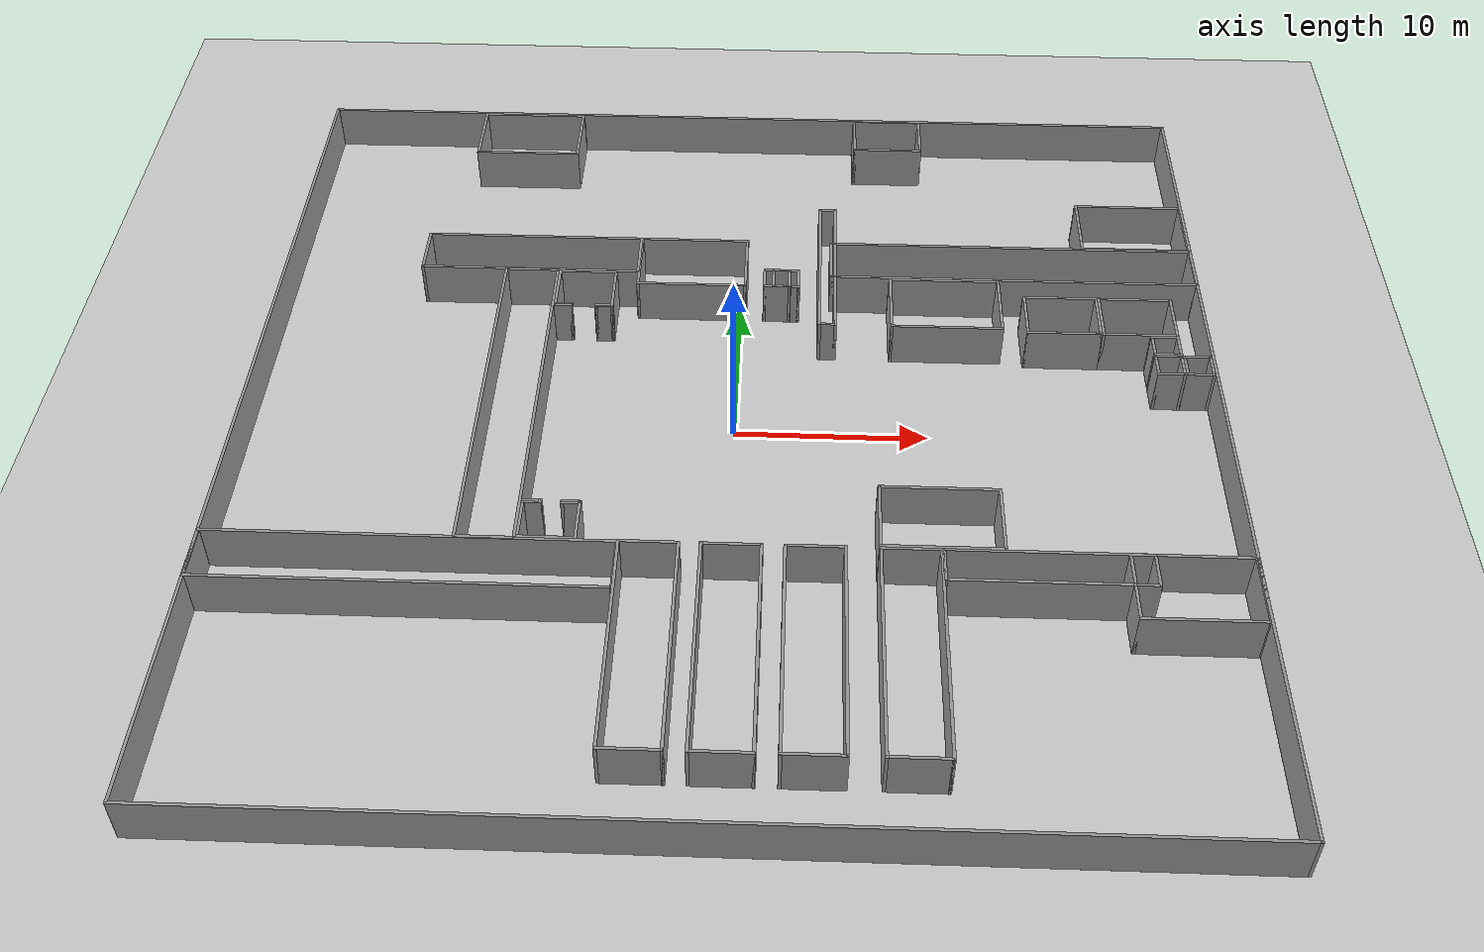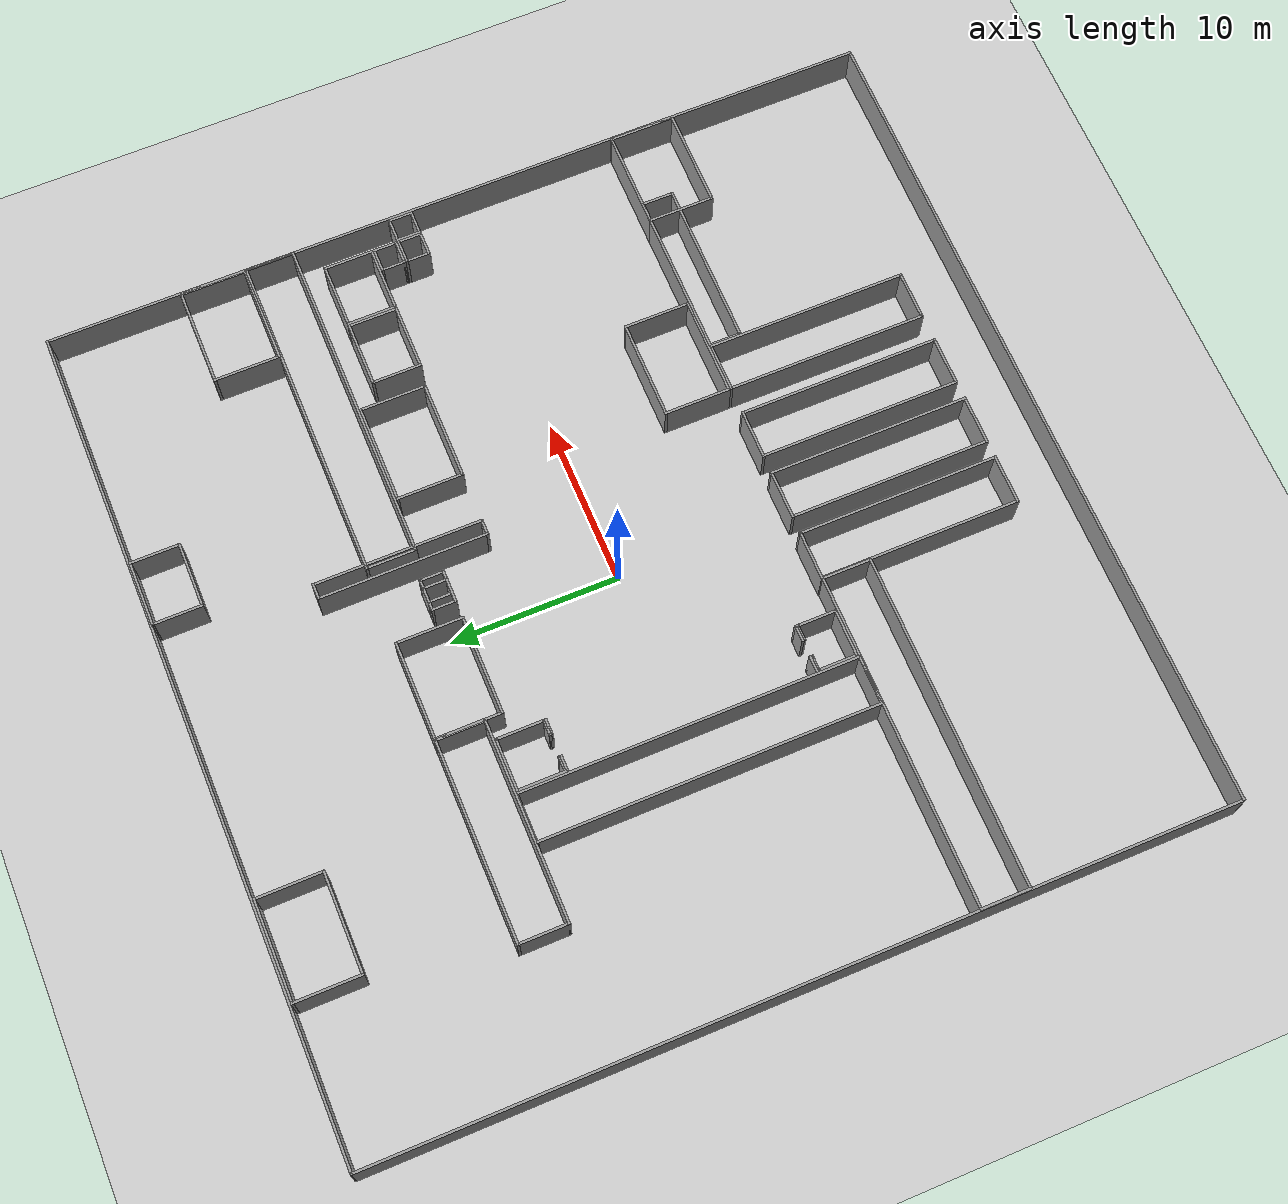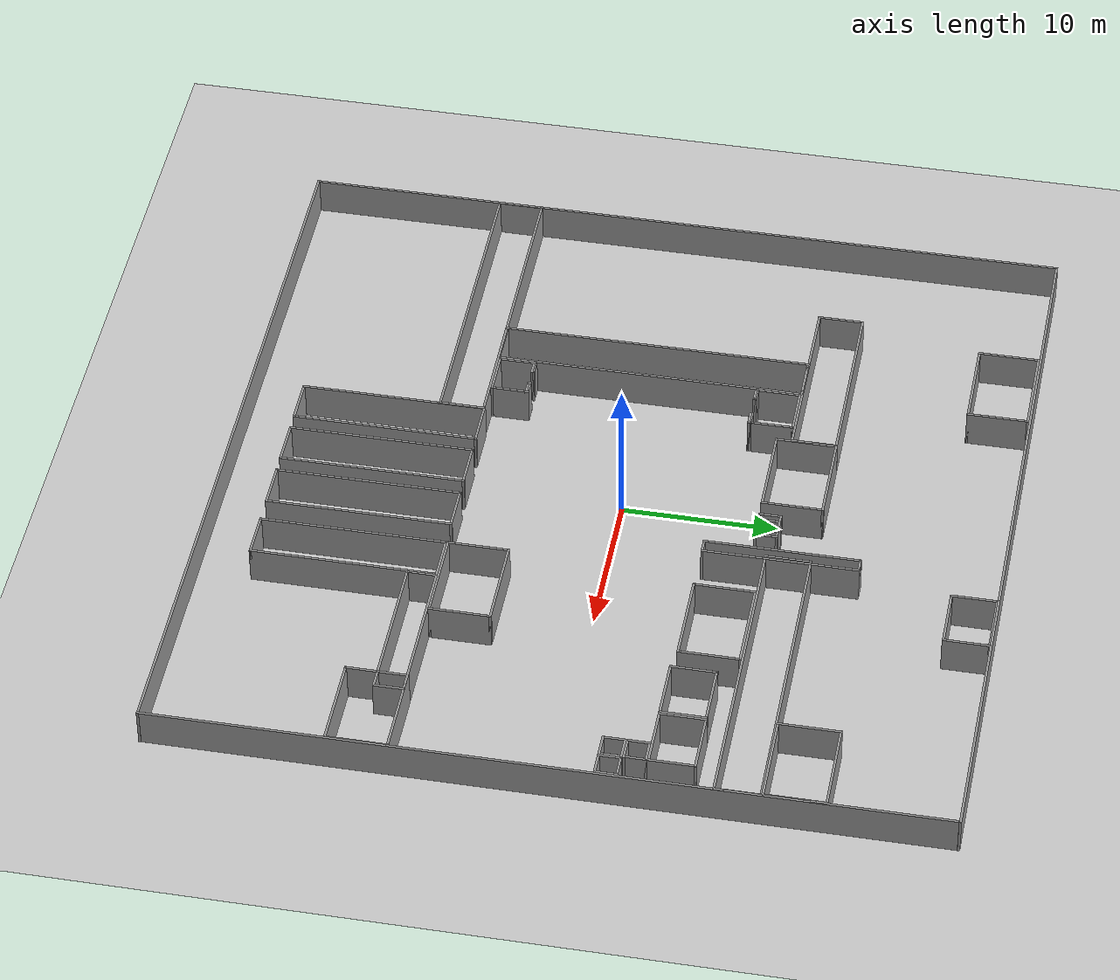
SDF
<sdf version="1.6">
 <world name="default">
  <light name="sun" type="directional">
   <pose>0 0 10 0 -0 0</pose>
   <diffuse>0.8 0.8 0.8 1</diffuse>
   <specular>0.2 0.2 0.2 1</specular>
   <attenuation>
    <range>1000</range>
    <constant>0.9</constant>
    <linear>0.01</linear>
    <quadratic>0.001</quadratic>
   </attenuation>
   <direction>-0.5 0.1 -0.9</direction>
  </light>
  <model name="ground_plane">
   <static>1</static>
   <link name="link">
    <collision name="collision">
     <geometry><plane><normal>0 0 1</normal><size>100 100</size></plane></geometry>
     <surface>
      <contact><collide_bitmask>65535</collide_bitmask></contact>
      <friction><ode><mu>100</mu><mu2>50</mu2></ode></friction>
     </surface>
    </collision>
    <visual name="visual">
     <cast_shadows>0</cast_shadows>
     <geometry><plane><normal>0 0 1</normal><size>100 100</size></plane></geometry>
     <material>
      <script><uri>file://media/materials/scripts/gazebo.material</uri><name>Gazebo/Grey</name></script>
     </material>
    </visual>
   </link>
  </model>
  <gravity>0 0 -9.8</gravity>
  <magnetic_field>6e-06 2.3e-05 -4.2e-05</magnetic_field>
  <atmosphere type="adiabatic"/>
  <physics name="default_physics" default="0" type="ode">
   <max_step_size>0.005</max_step_size>
   <real_time_factor>1</real_time_factor>
   <real_time_update_rate>200</real_time_update_rate>
  </physics>
  <scene><ambient>0.4 0.4 0.4 1</ambient><background>0.7 0.7 0.7 1</background><shadows>1</shadows></scene>
  <spherical_coordinates>
   <surface_model>EARTH_WGS84</surface_model>
   <latitude_deg>0</latitude_deg>
   <longitude_deg>0</longitude_deg>
   <elevation>0</elevation>
   <heading_deg>0</heading_deg>
  </spherical_coordinates>
  <model name="wall_50m_v">
   <pose>-25.0143 -0.23534 0 0 -0 0</pose>
   <link name="Wall_2">
    <collision name="Wall_2_Collision">
     <geometry><box><size>50 0.15 2.5</size></box></geometry>
     <pose>0 0 1.25 0 -0 0</pose>
    </collision>
    <visual name="Wall_2_Visual">
     <pose>0 0 1.25 0 -0 0</pose>
     <geometry><box><size>50 0.15 2.5</size></box></geometry>
     <material>
      <script><uri>file://media/materials/scripts/gazebo.material</uri><name>Gazebo/Grey</name></script>
      <ambient>1 1 1 1</ambient>
     </material>
     <meta><layer>0</layer></meta>
    </visual>
    <pose>-0 -1e-06 0 0 -0 -1.5708</pose>
   </link>
   <static>1</static>
  </model>
  <model name="wall_50m_0">
   <pose>-0.071935 -25.2621 0 0 -0 0</pose>
   <link name="Wall_0">
    <collision name="Wall_0_Collision">
     <geometry><box><size>50 0.15 2.5</size></box></geometry>
     <pose>0 0 1.25 0 -0 0</pose>
    </collision>
    <visual name="Wall_0_Visual">
     <pose>0 0 1.25 0 -0 0</pose>
     <geometry><box><size>50 0.15 2.5</size></box></geometry>
     <material>
      <script><uri>file://media/materials/scripts/gazebo.material</uri><name>Gazebo/Grey</name></script>
      <ambient>1 1 1 1</ambient>
     </material>
     <meta><layer>0</layer></meta>
    </visual>
    <pose>-1e-06 0 0 0 -0 0</pose>
   </link>
   <static>1</static>
  </model>
  <model name="wall_50m_1">
   <pose>-0.069466 24.7463 0 0 -0 0</pose>
   <link name="Wall_0">
    <collision name="Wall_0_Collision">
     <geometry><box><size>50 0.15 2.5</size></box></geometry>
     <pose>0 0 1.25 0 -0 0</pose>
    </collision>
    <visual name="Wall_0_Visual">
     <pose>0 0 1.25 0 -0 0</pose>
     <geometry><box><size>50 0.15 2.5</size></box></geometry>
     <material>
      <script><uri>file://media/materials/scripts/gazebo.material</uri><name>Gazebo/Grey</name></script>
      <ambient>1 1 1 1</ambient>
     </material>
     <meta><layer>0</layer></meta>
    </visual>
    <pose>-1e-06 0 0 0 -0 0</pose>
   </link>
   <static>1</static>
  </model>
  <model name="wall_50m_v_0">
   <pose>24.8495 -0.34033 0 0 -0 0</pose>
   <link name="Wall_2">
    <collision name="Wall_2_Collision">
     <geometry><box><size>50 0.15 2.5</size></box></geometry>
     <pose>0 0 1.25 0 -0 0</pose>
    </collision>
    <visual name="Wall_2_Visual">
     <pose>0 0 1.25 0 -0 0</pose>
     <geometry><box><size>50 0.15 2.5</size></box></geometry>
     <material>
      <script><uri>file://media/materials/scripts/gazebo.material</uri><name>Gazebo/Grey</name></script>
      <ambient>1 1 1 1</ambient>
     </material>
     <meta><layer>0</layer></meta>
    </visual>
    <pose>-0 -1e-06 0 0 -0 -1.5708</pose>
   </link>
   <static>1</static>
  </model>
  <model name="base20x3">
   <pose>-11.4278 0.026202 0 0 -0 0</pose>
   <link name="Wall_21">
    <collision name="Wall_21_Collision">
     <geometry><box><size>20 0.15 2.5</size></box></geometry>
     <pose>0 0 1.25 0 -0 0</pose>
    </collision>
    <visual name="Wall_21_Visual">
     <pose>0 0 1.25 0 -0 0</pose>
     <geometry><box><size>20 0.15 2.5</size></box></geometry>
     <material>
      <script><uri>file://media/materials/scripts/gazebo.material</uri><name>Gazebo/Grey</name></script>
      <ambient>1 1 1 1</ambient>
     </material>
     <meta><layer>0</layer></meta>
    </visual>
    <pose>-1.425 -0 0 0 -0 -1.5708</pose>
   </link>
   <link name="Wall_22">
    <collision name="Wall_22_Collision">
     <geometry><box><size>3 0.15 2.5</size></box></geometry>
     <pose>0 0 1.25 0 -0 0</pose>
    </collision>
    <visual name="Wall_22_Visual">
     <pose>0 0 1.25 0 -0 0</pose>
     <geometry><box><size>3 0.15 2.5</size></box></geometry>
     <material>
      <script><uri>file://media/materials/scripts/gazebo.material</uri><name>Gazebo/Grey</name></script>
      <ambient>1 1 1 1</ambient>
     </material>
     <meta><layer>0</layer></meta>
    </visual>
    <pose>-0 -9.925 0 0 -0 0</pose>
   </link>
   <link name="Wall_23">
    <collision name="Wall_23_Collision">
     <geometry><box><size>20 0.15 2.5</size></box></geometry>
     <pose>0 0 1.25 0 -0 0</pose>
    </collision>
    <visual name="Wall_23_Visual">
     <pose>0 0 1.25 0 -0 0</pose>
     <geometry><box><size>20 0.15 2.5</size></box></geometry>
     <material>
      <script><uri>file://media/materials/scripts/gazebo.material</uri><name>Gazebo/Grey</name></script>
      <ambient>1 1 1 1</ambient>
     </material>
     <meta><layer>0</layer></meta>
    </visual>
    <pose>1.425 -0 0 0 -0 1.5708</pose>
   </link>
   <link name="Wall_24">
    <collision name="Wall_24_Collision">
     <geometry><box><size>3 0.15 2.5</size></box></geometry>
     <pose>0 0 1.25 0 -0 0</pose>
    </collision>
    <visual name="Wall_24_Visual">
     <pose>0 0 1.25 0 -0 0</pose>
     <geometry><box><size>3 0.15 2.5</size></box></geometry>
     <material>
      <script><uri>file://media/materials/scripts/gazebo.material</uri><name>Gazebo/Grey</name></script>
      <ambient>1 1 1 1</ambient>
     </material>
     <meta><layer>0</layer></meta>
    </visual>
    <pose>-0 9.925 0 0 -0 3.14159</pose>
   </link>
   <static>1</static>
  </model>
  <model name="base3x20">
   <pose>-15.0546 -11.3706 0 0 -0 0</pose>
   <link name="Wall_16">
    <collision name="Wall_16_Collision">
     <geometry><box><size>3 0.15 2.5</size></box></geometry>
     <pose>0 0 1.25 0 -0 0</pose>
    </collision>
    <visual name="Wall_16_Visual">
     <pose>0 0 1.25 0 -0 0</pose>
     <geometry><box><size>3 0.15 2.5</size></box></geometry>
     <material>
      <script><uri>file://media/materials/scripts/gazebo.material</uri><name>Gazebo/Grey</name></script>
      <ambient>1 1 1 1</ambient>
     </material>
     <meta><layer>0</layer></meta>
    </visual>
    <pose>-9.925 -0 0 0 -0 -1.5708</pose>
   </link>
   <link name="Wall_17">
    <collision name="Wall_17_Collision">
     <geometry><box><size>20 0.15 2.5</size></box></geometry>
     <pose>0 0 1.25 0 -0 0</pose>
    </collision>
    <visual name="Wall_17_Visual">
     <pose>0 0 1.25 0 -0 0</pose>
     <geometry><box><size>20 0.15 2.5</size></box></geometry>
     <material>
      <script><uri>file://media/materials/scripts/gazebo.material</uri><name>Gazebo/Grey</name></script>
      <ambient>1 1 1 1</ambient>
     </material>
     <meta><layer>0</layer></meta>
    </visual>
    <pose>-0 -1.425 0 0 -0 0</pose>
   </link>
   <link name="Wall_18">
    <collision name="Wall_18_Collision">
     <geometry><box><size>3 0.15 2.5</size></box></geometry>
     <pose>0 0 1.25 0 -0 0</pose>
    </collision>
    <visual name="Wall_18_Visual">
     <pose>0 0 1.25 0 -0 0</pose>
     <geometry><box><size>3 0.15 2.5</size></box></geometry>
     <material>
      <script><uri>file://media/materials/scripts/gazebo.material</uri><name>Gazebo/Grey</name></script>
      <ambient>1 1 1 1</ambient>
     </material>
     <meta><layer>0</layer></meta>
    </visual>
    <pose>9.925 -0 0 0 -0 1.5708</pose>
   </link>
   <link name="Wall_19">
    <collision name="Wall_19_Collision">
     <geometry><box><size>20 0.15 2.5</size></box></geometry>
     <pose>0 0 1.25 0 -0 0</pose>
    </collision>
    <visual name="Wall_19_Visual">
     <pose>0 0 1.25 0 -0 0</pose>
     <geometry><box><size>20 0.15 2.5</size></box></geometry>
     <material>
      <script><uri>file://media/materials/scripts/gazebo.material</uri><name>Gazebo/Grey</name></script>
      <ambient>1 1 1 1</ambient>
     </material>
     <meta><layer>0</layer></meta>
    </visual>
    <pose>-0 1.425 0 0 -0 3.14159</pose>
   </link>
   <static>1</static>
  </model>
  <model name="base12x3">
   <pose>-3.65533 -15.8322 0 0 -0 0</pose>
   <link name="Wall_6">
    <collision name="Wall_6_Collision">
     <geometry><box><size>12 0.15 2.5</size></box></geometry>
     <pose>0 0 1.25 0 -0 0</pose>
    </collision>
    <visual name="Wall_6_Visual">
     <pose>0 0 1.25 0 -0 0</pose>
     <geometry><box><size>12 0.15 2.5</size></box></geometry>
     <material>
      <script><uri>file://media/materials/scripts/gazebo.material</uri><name>Gazebo/Grey</name></script>
      <ambient>1 1 1 1</ambient>
     </material>
     <meta><layer>0</layer></meta>
    </visual>
    <pose>-1.425 0 0 0 -0 -1.5708</pose>
   </link>
   <link name="Wall_7">
    <collision name="Wall_7_Collision">
     <geometry><box><size>3 0.15 2.5</size></box></geometry>
     <pose>0 0 1.25 0 -0 0</pose>
    </collision>
    <visual name="Wall_7_Visual">
     <pose>0 0 1.25 0 -0 0</pose>
     <geometry><box><size>3 0.15 2.5</size></box></geometry>
     <material>
      <script><uri>file://media/materials/scripts/gazebo.material</uri><name>Gazebo/Grey</name></script>
      <ambient>1 1 1 1</ambient>
     </material>
     <meta><layer>0</layer></meta>
    </visual>
    <pose>0 -5.925 0 0 -0 0</pose>
   </link>
   <link name="Wall_8">
    <collision name="Wall_8_Collision">
     <geometry><box><size>12 0.15 2.5</size></box></geometry>
     <pose>0 0 1.25 0 -0 0</pose>
    </collision>
    <visual name="Wall_8_Visual">
     <pose>0 0 1.25 0 -0 0</pose>
     <geometry><box><size>12 0.15 2.5</size></box></geometry>
     <material>
      <script><uri>file://media/materials/scripts/gazebo.material</uri><name>Gazebo/Grey</name></script>
      <ambient>1 1 1 1</ambient>
     </material>
     <meta><layer>0</layer></meta>
    </visual>
    <pose>1.425 0 0 0 -0 1.5708</pose>
   </link>
   <link name="Wall_9">
    <collision name="Wall_9_Collision">
     <geometry><box><size>3 0.15 2.5</size></box></geometry>
     <pose>0 0 1.25 0 -0 0</pose>
    </collision>
    <visual name="Wall_9_Visual">
     <pose>0 0 1.25 0 -0 0</pose>
     <geometry><box><size>3 0.15 2.5</size></box></geometry>
     <material>
      <script><uri>file://media/materials/scripts/gazebo.material</uri><name>Gazebo/Grey</name></script>
      <ambient>1 1 1 1</ambient>
     </material>
     <meta><layer>0</layer></meta>
    </visual>
    <pose>0 5.925 0 0 -0 3.14159</pose>
   </link>
   <static>1</static>
  </model>
  <model name="base12x3_0">
   <pose>0.25568 -15.8332 0 0 -0 0</pose>
   <link name="Wall_6">
    <collision name="Wall_6_Collision">
     <geometry><box><size>12 0.15 2.5</size></box></geometry>
     <pose>0 0 1.25 0 -0 0</pose>
    </collision>
    <visual name="Wall_6_Visual">
     <pose>0 0 1.25 0 -0 0</pose>
     <geometry><box><size>12 0.15 2.5</size></box></geometry>
     <material>
      <script><uri>file://media/materials/scripts/gazebo.material</uri><name>Gazebo/Grey</name></script>
      <ambient>1 1 1 1</ambient>
     </material>
     <meta><layer>0</layer></meta>
    </visual>
    <pose>-1.425 0 0 0 -0 -1.5708</pose>
   </link>
   <link name="Wall_7">
    <collision name="Wall_7_Collision">
     <geometry><box><size>3 0.15 2.5</size></box></geometry>
     <pose>0 0 1.25 0 -0 0</pose>
    </collision>
    <visual name="Wall_7_Visual">
     <pose>0 0 1.25 0 -0 0</pose>
     <geometry><box><size>3 0.15 2.5</size></box></geometry>
     <material>
      <script><uri>file://media/materials/scripts/gazebo.material</uri><name>Gazebo/Grey</name></script>
      <ambient>1 1 1 1</ambient>
     </material>
     <meta><layer>0</layer></meta>
    </visual>
    <pose>0 -5.925 0 0 -0 0</pose>
   </link>
   <link name="Wall_8">
    <collision name="Wall_8_Collision">
     <geometry><box><size>12 0.15 2.5</size></box></geometry>
     <pose>0 0 1.25 0 -0 0</pose>
    </collision>
    <visual name="Wall_8_Visual">
     <pose>0 0 1.25 0 -0 0</pose>
     <geometry><box><size>12 0.15 2.5</size></box></geometry>
     <material>
      <script><uri>file://media/materials/scripts/gazebo.material</uri><name>Gazebo/Grey</name></script>
      <ambient>1 1 1 1</ambient>
     </material>
     <meta><layer>0</layer></meta>
    </visual>
    <pose>1.425 0 0 0 -0 1.5708</pose>
   </link>
   <link name="Wall_9">
    <collision name="Wall_9_Collision">
     <geometry><box><size>3 0.15 2.5</size></box></geometry>
     <pose>0 0 1.25 0 -0 0</pose>
    </collision>
    <visual name="Wall_9_Visual">
     <pose>0 0 1.25 0 -0 0</pose>
     <geometry><box><size>3 0.15 2.5</size></box></geometry>
     <material>
      <script><uri>file://media/materials/scripts/gazebo.material</uri><name>Gazebo/Grey</name></script>
      <ambient>1 1 1 1</ambient>
     </material>
     <meta><layer>0</layer></meta>
    </visual>
    <pose>0 5.925 0 0 -0 3.14159</pose>
   </link>
   <static>1</static>
  </model>
  <model name="base12x3_1">
   <pose>4.21694 -15.8234 0 0 -0 0</pose>
   <link name="Wall_6">
    <collision name="Wall_6_Collision">
     <geometry><box><size>12 0.15 2.5</size></box></geometry>
     <pose>0 0 1.25 0 -0 0</pose>
    </collision>
    <visual name="Wall_6_Visual">
     <pose>0 0 1.25 0 -0 0</pose>
     <geometry><box><size>12 0.15 2.5</size></box></geometry>
     <material>
      <script><uri>file://media/materials/scripts/gazebo.material</uri><name>Gazebo/Grey</name></script>
      <ambient>1 1 1 1</ambient>
     </material>
     <meta><layer>0</layer></meta>
    </visual>
    <pose>-1.425 0 0 0 -0 -1.5708</pose>
   </link>
   <link name="Wall_7">
    <collision name="Wall_7_Collision">
     <geometry><box><size>3 0.15 2.5</size></box></geometry>
     <pose>0 0 1.25 0 -0 0</pose>
    </collision>
    <visual name="Wall_7_Visual">
     <pose>0 0 1.25 0 -0 0</pose>
     <geometry><box><size>3 0.15 2.5</size></box></geometry>
     <material>
      <script><uri>file://media/materials/scripts/gazebo.material</uri><name>Gazebo/Grey</name></script>
      <ambient>1 1 1 1</ambient>
     </material>
     <meta><layer>0</layer></meta>
    </visual>
    <pose>0 -5.925 0 0 -0 0</pose>
   </link>
   <link name="Wall_8">
    <collision name="Wall_8_Collision">
     <geometry><box><size>12 0.15 2.5</size></box></geometry>
     <pose>0 0 1.25 0 -0 0</pose>
    </collision>
    <visual name="Wall_8_Visual">
     <pose>0 0 1.25 0 -0 0</pose>
     <geometry><box><size>12 0.15 2.5</size></box></geometry>
     <material>
      <script><uri>file://media/materials/scripts/gazebo.material</uri><name>Gazebo/Grey</name></script>
      <ambient>1 1 1 1</ambient>
     </material>
     <meta><layer>0</layer></meta>
    </visual>
    <pose>1.425 0 0 0 -0 1.5708</pose>
   </link>
   <link name="Wall_9">
    <collision name="Wall_9_Collision">
     <geometry><box><size>3 0.15 2.5</size></box></geometry>
     <pose>0 0 1.25 0 -0 0</pose>
    </collision>
    <visual name="Wall_9_Visual">
     <pose>0 0 1.25 0 -0 0</pose>
     <geometry><box><size>3 0.15 2.5</size></box></geometry>
     <material>
      <script><uri>file://media/materials/scripts/gazebo.material</uri><name>Gazebo/Grey</name></script>
      <ambient>1 1 1 1</ambient>
     </material>
     <meta><layer>0</layer></meta>
    </visual>
    <pose>0 5.925 0 0 -0 3.14159</pose>
   </link>
   <static>1</static>
  </model>
  <model name="base12x3_2">
   <pose>8.71498 -15.8148 0 0 -0 0</pose>
   <link name="Wall_6">
    <collision name="Wall_6_Collision">
     <geometry><box><size>12 0.15 2.5</size></box></geometry>
     <pose>0 0 1.25 0 -0 0</pose>
    </collision>
    <visual name="Wall_6_Visual">
     <pose>0 0 1.25 0 -0 0</pose>
     <geometry><box><size>12 0.15 2.5</size></box></geometry>
     <material>
      <script><uri>file://media/materials/scripts/gazebo.material</uri><name>Gazebo/Grey</name></script>
      <ambient>1 1 1 1</ambient>
     </material>
     <meta><layer>0</layer></meta>
    </visual>
    <pose>-1.425 0 0 0 -0 -1.5708</pose>
   </link>
   <link name="Wall_7">
    <collision name="Wall_7_Collision">
     <geometry><box><size>3 0.15 2.5</size></box></geometry>
     <pose>0 0 1.25 0 -0 0</pose>
    </collision>
    <visual name="Wall_7_Visual">
     <pose>0 0 1.25 0 -0 0</pose>
     <geometry><box><size>3 0.15 2.5</size></box></geometry>
     <material>
      <script><uri>file://media/materials/scripts/gazebo.material</uri><name>Gazebo/Grey</name></script>
      <ambient>1 1 1 1</ambient>
     </material>
     <meta><layer>0</layer></meta>
    </visual>
    <pose>0 -5.925 0 0 -0 0</pose>
   </link>
   <link name="Wall_8">
    <collision name="Wall_8_Collision">
     <geometry><box><size>12 0.15 2.5</size></box></geometry>
     <pose>0 0 1.25 0 -0 0</pose>
    </collision>
    <visual name="Wall_8_Visual">
     <pose>0 0 1.25 0 -0 0</pose>
     <geometry><box><size>12 0.15 2.5</size></box></geometry>
     <material>
      <script><uri>file://media/materials/scripts/gazebo.material</uri><name>Gazebo/Grey</name></script>
      <ambient>1 1 1 1</ambient>
     </material>
     <meta><layer>0</layer></meta>
    </visual>
    <pose>1.425 0 0 0 -0 1.5708</pose>
   </link>
   <link name="Wall_9">
    <collision name="Wall_9_Collision">
     <geometry><box><size>3 0.15 2.5</size></box></geometry>
     <pose>0 0 1.25 0 -0 0</pose>
    </collision>
    <visual name="Wall_9_Visual">
     <pose>0 0 1.25 0 -0 0</pose>
     <geometry><box><size>3 0.15 2.5</size></box></geometry>
     <material>
      <script><uri>file://media/materials/scripts/gazebo.material</uri><name>Gazebo/Grey</name></script>
      <ambient>1 1 1 1</ambient>
     </material>
     <meta><layer>0</layer></meta>
    </visual>
    <pose>0 5.925 0 0 -0 3.14159</pose>
   </link>
   <static>1</static>
  </model>
  <model name="base2x10">
   <pose>15.1626 -10.8018 0 0 -0 0</pose>
   <link name="Wall_10">
    <collision name="Wall_10_Collision">
     <geometry><box><size>2 0.15 2.5</size></box></geometry>
     <pose>0 0 1.25 0 -0 0</pose>
    </collision>
    <visual name="Wall_10_Visual">
     <pose>0 0 1.25 0 -0 0</pose>
     <geometry><box><size>2 0.15 2.5</size></box></geometry>
     <material>
      <script><uri>file://media/materials/scripts/gazebo.material</uri><name>Gazebo/Grey</name></script>
      <ambient>1 1 1 1</ambient>
     </material>
     <meta><layer>0</layer></meta>
    </visual>
    <pose>-4.925 0 0 0 -0 -1.5708</pose>
   </link>
   <link name="Wall_11">
    <collision name="Wall_11_Collision">
     <geometry><box><size>10 0.15 2.5</size></box></geometry>
     <pose>0 0 1.25 0 -0 0</pose>
    </collision>
    <visual name="Wall_11_Visual">
     <pose>0 0 1.25 0 -0 0</pose>
     <geometry><box><size>10 0.15 2.5</size></box></geometry>
     <material>
      <script><uri>file://media/materials/scripts/gazebo.material</uri><name>Gazebo/Grey</name></script>
      <ambient>1 1 1 1</ambient>
     </material>
     <meta><layer>0</layer></meta>
    </visual>
    <pose>0 -0.925 0 0 -0 0</pose>
   </link>
   <link name="Wall_12">
    <collision name="Wall_12_Collision">
     <geometry><box><size>2 0.15 2.5</size></box></geometry>
     <pose>0 0 1.25 0 -0 0</pose>
    </collision>
    <visual name="Wall_12_Visual">
     <pose>0 0 1.25 0 -0 0</pose>
     <geometry><box><size>2 0.15 2.5</size></box></geometry>
     <material>
      <script><uri>file://media/materials/scripts/gazebo.material</uri><name>Gazebo/Grey</name></script>
      <ambient>1 1 1 1</ambient>
     </material>
     <meta><layer>0</layer></meta>
    </visual>
    <pose>4.925 0 0 0 -0 1.5708</pose>
   </link>
   <link name="Wall_13">
    <collision name="Wall_13_Collision">
     <geometry><box><size>10 0.15 2.5</size></box></geometry>
     <pose>0 0 1.25 0 -0 0</pose>
    </collision>
    <visual name="Wall_13_Visual">
     <pose>0 0 1.25 0 -0 0</pose>
     <geometry><box><size>10 0.15 2.5</size></box></geometry>
     <material>
      <script><uri>file://media/materials/scripts/gazebo.material</uri><name>Gazebo/Grey</name></script>
      <ambient>1 1 1 1</ambient>
     </material>
     <meta><layer>0</layer></meta>
    </visual>
    <pose>0 0.925 0 0 -0 3.14159</pose>
   </link>
   <static>1</static>
  </model>
  <model name="base4x6">
   <pose>21.8624 -11.7949 0 0 -0 0</pose>
   <link name="Wall_23">
    <collision name="Wall_23_Collision">
     <geometry><box><size>4 0.15 2.5</size></box></geometry>
     <pose>0 0 1.25 0 -0 0</pose>
    </collision>
    <visual name="Wall_23_Visual">
     <pose>0 0 1.25 0 -0 0</pose>
     <geometry><box><size>4 0.15 2.5</size></box></geometry>
     <material>
      <script><uri>file://media/materials/scripts/gazebo.material</uri><name>Gazebo/Grey</name></script>
      <ambient>1 1 1 1</ambient>
     </material>
     <meta><layer>0</layer></meta>
    </visual>
    <pose>-2.925 0 0 0 -0 -1.5708</pose>
   </link>
   <link name="Wall_24">
    <collision name="Wall_24_Collision">
     <geometry><box><size>6 0.15 2.5</size></box></geometry>
     <pose>0 0 1.25 0 -0 0</pose>
    </collision>
    <visual name="Wall_24_Visual">
     <pose>0 0 1.25 0 -0 0</pose>
     <geometry><box><size>6 0.15 2.5</size></box></geometry>
     <material>
      <script><uri>file://media/materials/scripts/gazebo.material</uri><name>Gazebo/Grey</name></script>
      <ambient>1 1 1 1</ambient>
     </material>
     <meta><layer>0</layer></meta>
    </visual>
    <pose>-0 -1.925 0 0 -0 0</pose>
   </link>
   <link name="Wall_25">
    <collision name="Wall_25_Collision">
     <geometry><box><size>4 0.15 2.5</size></box></geometry>
     <pose>0 0 1.25 0 -0 0</pose>
    </collision>
    <visual name="Wall_25_Visual">
     <pose>0 0 1.25 0 -0 0</pose>
     <geometry><box><size>4 0.15 2.5</size></box></geometry>
     <material>
      <script><uri>file://media/materials/scripts/gazebo.material</uri><name>Gazebo/Grey</name></script>
      <ambient>1 1 1 1</ambient>
     </material>
     <meta><layer>0</layer></meta>
    </visual>
    <pose>2.925 0 0 0 -0 1.5708</pose>
   </link>
   <link name="Wall_26">
    <collision name="Wall_26_Collision">
     <geometry><box><size>6 0.15 2.5</size></box></geometry>
     <pose>0 0 1.25 0 -0 0</pose>
    </collision>
    <visual name="Wall_26_Visual">
     <pose>0 0 1.25 0 -0 0</pose>
     <geometry><box><size>6 0.15 2.5</size></box></geometry>
     <material>
      <script><uri>file://media/materials/scripts/gazebo.material</uri><name>Gazebo/Grey</name></script>
      <ambient>1 1 1 1</ambient>
     </material>
     <meta><layer>0</layer></meta>
    </visual>
    <pose>-0 1.925 0 0 -0 3.14159</pose>
   </link>
   <static>1</static>
  </model>
  <model name="base3x12">
   <pose>-11.5553 11.4309 0 0 -0 0</pose>
   <link name="Wall_0">
    <collision name="Wall_0_Collision">
     <geometry><box><size>3 0.15 2.5</size></box></geometry>
     <pose>0 0 1.25 0 -0 0</pose>
    </collision>
    <visual name="Wall_0_Visual">
     <pose>0 0 1.25 0 -0 0</pose>
     <geometry><box><size>3 0.15 2.5</size></box></geometry>
     <material>
      <script><uri>file://media/materials/scripts/gazebo.material</uri><name>Gazebo/Grey</name></script>
      <ambient>1 1 1 1</ambient>
     </material>
     <meta><layer>0</layer></meta>
    </visual>
    <pose>-5.925 0 0 0 -0 -1.5708</pose>
   </link>
   <link name="Wall_1">
    <collision name="Wall_1_Collision">
     <geometry><box><size>12 0.15 2.5</size></box></geometry>
     <pose>0 0 1.25 0 -0 0</pose>
    </collision>
    <visual name="Wall_1_Visual">
     <pose>0 0 1.25 0 -0 0</pose>
     <geometry><box><size>12 0.15 2.5</size></box></geometry>
     <material>
      <script><uri>file://media/materials/scripts/gazebo.material</uri><name>Gazebo/Grey</name></script>
      <ambient>1 1 1 1</ambient>
     </material>
     <meta><layer>0</layer></meta>
    </visual>
    <pose>0 -1.425 0 0 -0 0</pose>
   </link>
   <link name="Wall_2">
    <collision name="Wall_2_Collision">
     <geometry><box><size>3 0.15 2.5</size></box></geometry>
     <pose>0 0 1.25 0 -0 0</pose>
    </collision>
    <visual name="Wall_2_Visual">
     <pose>0 0 1.25 0 -0 0</pose>
     <geometry><box><size>3 0.15 2.5</size></box></geometry>
     <material>
      <script><uri>file://media/materials/scripts/gazebo.material</uri><name>Gazebo/Grey</name></script>
      <ambient>1 1 1 1</ambient>
     </material>
     <meta><layer>0</layer></meta>
    </visual>
    <pose>5.925 0 0 0 -0 1.5708</pose>
   </link>
   <link name="Wall_3">
    <collision name="Wall_3_Collision">
     <geometry><box><size>12 0.15 2.5</size></box></geometry>
     <pose>0 0 1.25 0 -0 0</pose>
    </collision>
    <visual name="Wall_3_Visual">
     <pose>0 0 1.25 0 -0 0</pose>
     <geometry><box><size>12 0.15 2.5</size></box></geometry>
     <material>
      <script><uri>file://media/materials/scripts/gazebo.material</uri><name>Gazebo/Grey</name></script>
      <ambient>1 1 1 1</ambient>
     </material>
     <meta><layer>0</layer></meta>
    </visual>
    <pose>0 1.425 0 0 -0 3.14159</pose>
   </link>
   <static>1</static>
  </model>
  <model name="base3x20_1">
   <pose>14.8975 11.3894 0 0 -0 0</pose>
   <link name="Wall_16">
    <collision name="Wall_16_Collision">
     <geometry><box><size>3 0.15 2.5</size></box></geometry>
     <pose>0 0 1.25 0 -0 0</pose>
    </collision>
    <visual name="Wall_16_Visual">
     <pose>0 0 1.25 0 -0 0</pose>
     <geometry><box><size>3 0.15 2.5</size></box></geometry>
     <material>
      <script><uri>file://media/materials/scripts/gazebo.material</uri><name>Gazebo/Grey</name></script>
      <ambient>1 1 1 1</ambient>
     </material>
     <meta><layer>0</layer></meta>
    </visual>
    <pose>-9.925 -0 0 0 -0 -1.5708</pose>
   </link>
   <link name="Wall_17">
    <collision name="Wall_17_Collision">
     <geometry><box><size>20 0.15 2.5</size></box></geometry>
     <pose>0 0 1.25 0 -0 0</pose>
    </collision>
    <visual name="Wall_17_Visual">
     <pose>0 0 1.25 0 -0 0</pose>
     <geometry><box><size>20 0.15 2.5</size></box></geometry>
     <material>
      <script><uri>file://media/materials/scripts/gazebo.material</uri><name>Gazebo/Grey</name></script>
      <ambient>1 1 1 1</ambient>
     </material>
     <meta><layer>0</layer></meta>
    </visual>
    <pose>-0 -1.425 0 0 -0 0</pose>
   </link>
   <link name="Wall_18">
    <collision name="Wall_18_Collision">
     <geometry><box><size>3 0.15 2.5</size></box></geometry>
     <pose>0 0 1.25 0 -0 0</pose>
    </collision>
    <visual name="Wall_18_Visual">
     <pose>0 0 1.25 0 -0 0</pose>
     <geometry><box><size>3 0.15 2.5</size></box></geometry>
     <material>
      <script><uri>file://media/materials/scripts/gazebo.material</uri><name>Gazebo/Grey</name></script>
      <ambient>1 1 1 1</ambient>
     </material>
     <meta><layer>0</layer></meta>
    </visual>
    <pose>9.925 -0 0 0 -0 1.5708</pose>
   </link>
   <link name="Wall_19">
    <collision name="Wall_19_Collision">
     <geometry><box><size>20 0.15 2.5</size></box></geometry>
     <pose>0 0 1.25 0 -0 0</pose>
    </collision>
    <visual name="Wall_19_Visual">
     <pose>0 0 1.25 0 -0 0</pose>
     <geometry><box><size>20 0.15 2.5</size></box></geometry>
     <material>
      <script><uri>file://media/materials/scripts/gazebo.material</uri><name>Gazebo/Grey</name></script>
      <ambient>1 1 1 1</ambient>
     </material>
     <meta><layer>0</layer></meta>
    </visual>
    <pose>-0 1.425 0 0 -0 3.14159</pose>
   </link>
   <static>1</static>
  </model>
  <model name="base4x6_0">
   <pose>-2.63284 10.9342 0 0 -0 0</pose>
   <link name="Wall_23">
    <collision name="Wall_23_Collision">
     <geometry><box><size>4 0.15 2.5</size></box></geometry>
     <pose>0 0 1.25 0 -0 0</pose>
    </collision>
    <visual name="Wall_23_Visual">
     <pose>0 0 1.25 0 -0 0</pose>
     <geometry><box><size>4 0.15 2.5</size></box></geometry>
     <material>
      <script><uri>file://media/materials/scripts/gazebo.material</uri><name>Gazebo/Grey</name></script>
      <ambient>1 1 1 1</ambient>
     </material>
     <meta><layer>0</layer></meta>
    </visual>
    <pose>-2.925 0 0 0 -0 -1.5708</pose>
   </link>
   <link name="Wall_24">
    <collision name="Wall_24_Collision">
     <geometry><box><size>6 0.15 2.5</size></box></geometry>
     <pose>0 0 1.25 0 -0 0</pose>
    </collision>
    <visual name="Wall_24_Visual">
     <pose>0 0 1.25 0 -0 0</pose>
     <geometry><box><size>6 0.15 2.5</size></box></geometry>
     <material>
      <script><uri>file://media/materials/scripts/gazebo.material</uri><name>Gazebo/Grey</name></script>
      <ambient>1 1 1 1</ambient>
     </material>
     <meta><layer>0</layer></meta>
    </visual>
    <pose>-0 -1.925 0 0 -0 0</pose>
   </link>
   <link name="Wall_25">
    <collision name="Wall_25_Collision">
     <geometry><box><size>4 0.15 2.5</size></box></geometry>
     <pose>0 0 1.25 0 -0 0</pose>
    </collision>
    <visual name="Wall_25_Visual">
     <pose>0 0 1.25 0 -0 0</pose>
     <geometry><box><size>4 0.15 2.5</size></box></geometry>
     <material>
      <script><uri>file://media/materials/scripts/gazebo.material</uri><name>Gazebo/Grey</name></script>
      <ambient>1 1 1 1</ambient>
     </material>
     <meta><layer>0</layer></meta>
    </visual>
    <pose>2.925 0 0 0 -0 1.5708</pose>
   </link>
   <link name="Wall_26">
    <collision name="Wall_26_Collision">
     <geometry><box><size>6 0.15 2.5</size></box></geometry>
     <pose>0 0 1.25 0 -0 0</pose>
    </collision>
    <visual name="Wall_26_Visual">
     <pose>0 0 1.25 0 -0 0</pose>
     <geometry><box><size>6 0.15 2.5</size></box></geometry>
     <material>
      <script><uri>file://media/materials/scripts/gazebo.material</uri><name>Gazebo/Grey</name></script>
      <ambient>1 1 1 1</ambient>
     </material>
     <meta><layer>0</layer></meta>
    </visual>
    <pose>-0 1.925 0 0 -0 3.14159</pose>
   </link>
   <static>1</static>
  </model>
  <model name="base4x6_1">
   <pose>21.851 14.8303 0 0 -0 0</pose>
   <link name="Wall_23">
    <collision name="Wall_23_Collision">
     <geometry><box><size>4 0.15 2.5</size></box></geometry>
     <pose>0 0 1.25 0 -0 0</pose>
    </collision>
    <visual name="Wall_23_Visual">
     <pose>0 0 1.25 0 -0 0</pose>
     <geometry><box><size>4 0.15 2.5</size></box></geometry>
     <material>
      <script><uri>file://media/materials/scripts/gazebo.material</uri><name>Gazebo/Grey</name></script>
      <ambient>1 1 1 1</ambient>
     </material>
     <meta><layer>0</layer></meta>
    </visual>
    <pose>-2.925 0 0 0 -0 -1.5708</pose>
   </link>
   <link name="Wall_24">
    <collision name="Wall_24_Collision">
     <geometry><box><size>6 0.15 2.5</size></box></geometry>
     <pose>0 0 1.25 0 -0 0</pose>
    </collision>
    <visual name="Wall_24_Visual">
     <pose>0 0 1.25 0 -0 0</pose>
     <geometry><box><size>6 0.15 2.5</size></box></geometry>
     <material>
      <script><uri>file://media/materials/scripts/gazebo.material</uri><name>Gazebo/Grey</name></script>
      <ambient>1 1 1 1</ambient>
     </material>
     <meta><layer>0</layer></meta>
    </visual>
    <pose>-0 -1.925 0 0 -0 0</pose>
   </link>
   <link name="Wall_25">
    <collision name="Wall_25_Collision">
     <geometry><box><size>4 0.15 2.5</size></box></geometry>
     <pose>0 0 1.25 0 -0 0</pose>
    </collision>
    <visual name="Wall_25_Visual">
     <pose>0 0 1.25 0 -0 0</pose>
     <geometry><box><size>4 0.15 2.5</size></box></geometry>
     <material>
      <script><uri>file://media/materials/scripts/gazebo.material</uri><name>Gazebo/Grey</name></script>
      <ambient>1 1 1 1</ambient>
     </material>
     <meta><layer>0</layer></meta>
    </visual>
    <pose>2.925 0 0 0 -0 1.5708</pose>
   </link>
   <link name="Wall_26">
    <collision name="Wall_26_Collision">
     <geometry><box><size>6 0.15 2.5</size></box></geometry>
     <pose>0 0 1.25 0 -0 0</pose>
    </collision>
    <visual name="Wall_26_Visual">
     <pose>0 0 1.25 0 -0 0</pose>
     <geometry><box><size>6 0.15 2.5</size></box></geometry>
     <material>
      <script><uri>file://media/materials/scripts/gazebo.material</uri><name>Gazebo/Grey</name></script>
      <ambient>1 1 1 1</ambient>
     </material>
     <meta><layer>0</layer></meta>
    </visual>
    <pose>-0 1.925 0 0 -0 3.14159</pose>
   </link>
   <static>1</static>
  </model>
  <model name="base4x6_3">
   <pose>-12.9593 22.6793 0 0 -0 0</pose>
   <link name="Wall_23">
    <collision name="Wall_23_Collision">
     <geometry><box><size>4 0.15 2.5</size></box></geometry>
     <pose>0 0 1.25 0 -0 0</pose>
    </collision>
    <visual name="Wall_23_Visual">
     <pose>0 0 1.25 0 -0 0</pose>
     <geometry><box><size>4 0.15 2.5</size></box></geometry>
     <material>
      <script><uri>file://media/materials/scripts/gazebo.material</uri><name>Gazebo/Grey</name></script>
      <ambient>1 1 1 1</ambient>
     </material>
     <meta><layer>0</layer></meta>
    </visual>
    <pose>-2.925 0 0 0 -0 -1.5708</pose>
   </link>
   <link name="Wall_24">
    <collision name="Wall_24_Collision">
     <geometry><box><size>6 0.15 2.5</size></box></geometry>
     <pose>0 0 1.25 0 -0 0</pose>
    </collision>
    <visual name="Wall_24_Visual">
     <pose>0 0 1.25 0 -0 0</pose>
     <geometry><box><size>6 0.15 2.5</size></box></geometry>
     <material>
      <script><uri>file://media/materials/scripts/gazebo.material</uri><name>Gazebo/Grey</name></script>
      <ambient>1 1 1 1</ambient>
     </material>
     <meta><layer>0</layer></meta>
    </visual>
    <pose>-0 -1.925 0 0 -0 0</pose>
   </link>
   <link name="Wall_25">
    <collision name="Wall_25_Collision">
     <geometry><box><size>4 0.15 2.5</size></box></geometry>
     <pose>0 0 1.25 0 -0 0</pose>
    </collision>
    <visual name="Wall_25_Visual">
     <pose>0 0 1.25 0 -0 0</pose>
     <geometry><box><size>4 0.15 2.5</size></box></geometry>
     <material>
      <script><uri>file://media/materials/scripts/gazebo.material</uri><name>Gazebo/Grey</name></script>
      <ambient>1 1 1 1</ambient>
     </material>
     <meta><layer>0</layer></meta>
    </visual>
    <pose>2.925 0 0 0 -0 1.5708</pose>
   </link>
   <link name="Wall_26">
    <collision name="Wall_26_Collision">
     <geometry><box><size>6 0.15 2.5</size></box></geometry>
     <pose>0 0 1.25 0 -0 0</pose>
    </collision>
    <visual name="Wall_26_Visual">
     <pose>0 0 1.25 0 -0 0</pose>
     <geometry><box><size>6 0.15 2.5</size></box></geometry>
     <material>
      <script><uri>file://media/materials/scripts/gazebo.material</uri><name>Gazebo/Grey</name></script>
      <ambient>1 1 1 1</ambient>
     </material>
     <meta><layer>0</layer></meta>
    </visual>
    <pose>-0 1.925 0 0 -0 3.14159</pose>
   </link>
   <static>1</static>
  </model>
  <model name="base4x6_5">
   <pose>10.2051 -7.82544 0 0 -0 0</pose>
   <link name="Wall_23">
    <collision name="Wall_23_Collision">
     <geometry><box><size>4 0.15 2.5</size></box></geometry>
     <pose>0 0 1.25 0 -0 0</pose>
    </collision>
    <visual name="Wall_23_Visual">
     <pose>0 0 1.25 0 -0 0</pose>
     <geometry><box><size>4 0.15 2.5</size></box></geometry>
     <material>
      <script><uri>file://media/materials/scripts/gazebo.material</uri><name>Gazebo/Grey</name></script>
      <ambient>1 1 1 1</ambient>
     </material>
     <meta><layer>0</layer></meta>
    </visual>
    <pose>-2.925 0 0 0 -0 -1.5708</pose>
   </link>
   <link name="Wall_24">
    <collision name="Wall_24_Collision">
     <geometry><box><size>6 0.15 2.5</size></box></geometry>
     <pose>0 0 1.25 0 -0 0</pose>
    </collision>
    <visual name="Wall_24_Visual">
     <pose>0 0 1.25 0 -0 0</pose>
     <geometry><box><size>6 0.15 2.5</size></box></geometry>
     <material>
      <script><uri>file://media/materials/scripts/gazebo.material</uri><name>Gazebo/Grey</name></script>
      <ambient>1 1 1 1</ambient>
     </material>
     <meta><layer>0</layer></meta>
    </visual>
    <pose>-0 -1.925 0 0 -0 0</pose>
   </link>
   <link name="Wall_25">
    <collision name="Wall_25_Collision">
     <geometry><box><size>4 0.15 2.5</size></box></geometry>
     <pose>0 0 1.25 0 -0 0</pose>
    </collision>
    <visual name="Wall_25_Visual">
     <pose>0 0 1.25 0 -0 0</pose>
     <geometry><box><size>4 0.15 2.5</size></box></geometry>
     <material>
      <script><uri>file://media/materials/scripts/gazebo.material</uri><name>Gazebo/Grey</name></script>
      <ambient>1 1 1 1</ambient>
     </material>
     <meta><layer>0</layer></meta>
    </visual>
    <pose>2.925 0 0 0 -0 1.5708</pose>
   </link>
   <link name="Wall_26">
    <collision name="Wall_26_Collision">
     <geometry><box><size>6 0.15 2.5</size></box></geometry>
     <pose>0 0 1.25 0 -0 0</pose>
    </collision>
    <visual name="Wall_26_Visual">
     <pose>0 0 1.25 0 -0 0</pose>
     <geometry><box><size>6 0.15 2.5</size></box></geometry>
     <material>
      <script><uri>file://media/materials/scripts/gazebo.material</uri><name>Gazebo/Grey</name></script>
      <ambient>1 1 1 1</ambient>
     </material>
     <meta><layer>0</layer></meta>
    </visual>
    <pose>-0 1.925 0 0 -0 3.14159</pose>
   </link>
   <static>1</static>
  </model>
  <model name="base3x4_1">
   <pose>8.29177 23.232 0 0 -0 0</pose>
   <link name="Wall_18">
    <collision name="Wall_18_Collision">
     <geometry><box><size>3 0.15 2.5</size></box></geometry>
     <pose>0 0 1.25 0 -0 0</pose>
    </collision>
    <visual name="Wall_18_Visual">
     <pose>0 0 1.25 0 -0 0</pose>
     <geometry><box><size>3 0.15 2.5</size></box></geometry>
     <material>
      <script><uri>file://media/materials/scripts/gazebo.material</uri><name>Gazebo/Grey</name></script>
      <ambient>1 1 1 1</ambient>
     </material>
     <meta><layer>0</layer></meta>
    </visual>
    <pose>-1.925 -0 0 0 -0 -1.5708</pose>
   </link>
   <link name="Wall_19">
    <collision name="Wall_19_Collision">
     <geometry><box><size>4 0.15 2.5</size></box></geometry>
     <pose>0 0 1.25 0 -0 0</pose>
    </collision>
    <visual name="Wall_19_Visual">
     <pose>0 0 1.25 0 -0 0</pose>
     <geometry><box><size>4 0.15 2.5</size></box></geometry>
     <material>
      <script><uri>file://media/materials/scripts/gazebo.material</uri><name>Gazebo/Grey</name></script>
      <ambient>1 1 1 1</ambient>
     </material>
     <meta><layer>0</layer></meta>
    </visual>
    <pose>-0 -1.425 0 0 -0 0</pose>
   </link>
   <link name="Wall_20">
    <collision name="Wall_20_Collision">
     <geometry><box><size>3 0.15 2.5</size></box></geometry>
     <pose>0 0 1.25 0 -0 0</pose>
    </collision>
    <visual name="Wall_20_Visual">
     <pose>0 0 1.25 0 -0 0</pose>
     <geometry><box><size>3 0.15 2.5</size></box></geometry>
     <material>
      <script><uri>file://media/materials/scripts/gazebo.material</uri><name>Gazebo/Grey</name></script>
      <ambient>1 1 1 1</ambient>
     </material>
     <meta><layer>0</layer></meta>
    </visual>
    <pose>1.925 -0 0 0 -0 1.5708</pose>
   </link>
   <link name="Wall_21">
    <collision name="Wall_21_Collision">
     <geometry><box><size>4 0.15 2.5</size></box></geometry>
     <pose>0 0 1.25 0 -0 0</pose>
    </collision>
    <visual name="Wall_21_Visual">
     <pose>0 0 1.25 0 -0 0</pose>
     <geometry><box><size>4 0.15 2.5</size></box></geometry>
     <material>
      <script><uri>file://media/materials/scripts/gazebo.material</uri><name>Gazebo/Grey</name></script>
      <ambient>1 1 1 1</ambient>
     </material>
     <meta><layer>0</layer></meta>
    </visual>
    <pose>-0 1.425 0 0 -0 3.14159</pose>
   </link>
   <static>1</static>
  </model>
  <model name="base10x1_0">
   <pose>4.76084 10.9128 0 0 -0 0</pose>
   <link name="Wall_15">
    <collision name="Wall_15_Collision">
     <geometry><box><size>10 0.15 2.5</size></box></geometry>
     <pose>0 0 1.25 0 -0 0</pose>
    </collision>
    <visual name="Wall_15_Visual">
     <pose>0 0 1.25 0 -0 0</pose>
     <geometry><box><size>10 0.15 2.5</size></box></geometry>
     <material>
      <script><uri>file://media/materials/scripts/gazebo.material</uri><name>Gazebo/Grey</name></script>
      <ambient>1 1 1 1</ambient>
     </material>
     <meta><layer>0</layer></meta>
    </visual>
    <pose>-0.425 0 0 0 -0 1.5708</pose>
   </link>
   <link name="Wall_16">
    <collision name="Wall_16_Collision">
     <geometry><box><size>1 0.15 2.5</size></box></geometry>
     <pose>0 0 1.25 0 -0 0</pose>
    </collision>
    <visual name="Wall_16_Visual">
     <pose>0 0 1.25 0 -0 0</pose>
     <geometry><box><size>1 0.15 2.5</size></box></geometry>
     <material>
      <script><uri>file://media/materials/scripts/gazebo.material</uri><name>Gazebo/Grey</name></script>
      <ambient>1 1 1 1</ambient>
     </material>
     <meta><layer>0</layer></meta>
    </visual>
    <pose>0 4.925 0 0 -0 0</pose>
   </link>
   <link name="Wall_17">
    <collision name="Wall_17_Collision">
     <geometry><box><size>10 0.15 2.5</size></box></geometry>
     <pose>0 0 1.25 0 -0 0</pose>
    </collision>
    <visual name="Wall_17_Visual">
     <pose>0 0 1.25 0 -0 0</pose>
     <geometry><box><size>10 0.15 2.5</size></box></geometry>
     <material>
      <script><uri>file://media/materials/scripts/gazebo.material</uri><name>Gazebo/Grey</name></script>
      <ambient>1 1 1 1</ambient>
     </material>
     <meta><layer>0</layer></meta>
    </visual>
    <pose>0.425 0 0 0 -0 -1.5708</pose>
   </link>
   <link name="Wall_18">
    <collision name="Wall_18_Collision">
     <geometry><box><size>1 0.15 2.5</size></box></geometry>
     <pose>0 0 1.25 0 -0 0</pose>
    </collision>
    <visual name="Wall_18_Visual">
     <pose>0 0 1.25 0 -0 0</pose>
     <geometry><box><size>1 0.15 2.5</size></box></geometry>
     <material>
      <script><uri>file://media/materials/scripts/gazebo.material</uri><name>Gazebo/Grey</name></script>
      <ambient>1 1 1 1</ambient>
     </material>
     <meta><layer>0</layer></meta>
    </visual>
    <pose>0 -4.925 0 0 -0 3.14159</pose>
   </link>
   <static>1</static>
  </model>
  <model name="box_1.5mx1.5m">
   <pose>2.01566 9.69372 0 0 -0 0</pose>
   <link name="Wall_15">
    <collision name="Wall_15_Collision">
     <geometry><box><size>1.5 0.15 2.5</size></box></geometry>
     <pose>0 0 1.25 0 -0 0</pose>
    </collision>
    <visual name="Wall_15_Visual">
     <pose>0 0 1.25 0 -0 0</pose>
     <geometry><box><size>1.5 0.15 2.5</size></box></geometry>
     <material>
      <script><uri>file://media/materials/scripts/gazebo.material</uri><name>Gazebo/Grey</name></script>
      <ambient>1 1 1 1</ambient>
     </material>
     <meta><layer>0</layer></meta>
    </visual>
    <pose>-0.675 -0 0 0 -0 -1.5708</pose>
   </link>
   <link name="Wall_16">
    <collision name="Wall_16_Collision">
     <geometry><box><size>1.5 0.15 2.5</size></box></geometry>
     <pose>0 0 1.25 0 -0 0</pose>
    </collision>
    <visual name="Wall_16_Visual">
     <pose>0 0 1.25 0 -0 0</pose>
     <geometry><box><size>1.5 0.15 2.5</size></box></geometry>
     <material>
      <script><uri>file://media/materials/scripts/gazebo.material</uri><name>Gazebo/Grey</name></script>
      <ambient>1 1 1 1</ambient>
     </material>
     <meta><layer>0</layer></meta>
    </visual>
    <pose>-0 -0.675 0 0 -0 0</pose>
   </link>
   <link name="Wall_17">
    <collision name="Wall_17_Collision">
     <geometry><box><size>1.5 0.15 2.5</size></box></geometry>
     <pose>0 0 1.25 0 -0 0</pose>
    </collision>
    <visual name="Wall_17_Visual">
     <pose>0 0 1.25 0 -0 0</pose>
     <geometry><box><size>1.5 0.15 2.5</size></box></geometry>
     <material>
      <script><uri>file://media/materials/scripts/gazebo.material</uri><name>Gazebo/Grey</name></script>
      <ambient>1 1 1 1</ambient>
     </material>
     <meta><layer>0</layer></meta>
    </visual>
    <pose>0.675 -0 0 0 -0 1.5708</pose>
   </link>
   <link name="Wall_18">
    <collision name="Wall_18_Collision">
     <geometry><box><size>1.5 0.15 2.5</size></box></geometry>
     <pose>0 0 1.25 0 -0 0</pose>
    </collision>
    <visual name="Wall_18_Visual">
     <pose>0 0 1.25 0 -0 0</pose>
     <geometry><box><size>1.5 0.15 2.5</size></box></geometry>
     <material>
      <script><uri>file://media/materials/scripts/gazebo.material</uri><name>Gazebo/Grey</name></script>
      <ambient>1 1 1 1</ambient>
     </material>
     <meta><layer>0</layer></meta>
    </visual>
    <pose>-0 0.675 0 0 -0 3.14159</pose>
   </link>
   <static>1</static>
  </model>
  <model name="box_1.5mx1.5m_0">
   <pose>2.50923 9.69521 0 0 -0 0</pose>
   <link name="Wall_15">
    <collision name="Wall_15_Collision">
     <geometry><box><size>1.5 0.15 2.5</size></box></geometry>
     <pose>0 0 1.25 0 -0 0</pose>
    </collision>
    <visual name="Wall_15_Visual">
     <pose>0 0 1.25 0 -0 0</pose>
     <geometry><box><size>1.5 0.15 2.5</size></box></geometry>
     <material>
      <script><uri>file://media/materials/scripts/gazebo.material</uri><name>Gazebo/Grey</name></script>
      <ambient>1 1 1 1</ambient>
     </material>
     <meta><layer>0</layer></meta>
    </visual>
    <pose>-0.675 -0 0 0 -0 -1.5708</pose>
   </link>
   <link name="Wall_16">
    <collision name="Wall_16_Collision">
     <geometry><box><size>1.5 0.15 2.5</size></box></geometry>
     <pose>0 0 1.25 0 -0 0</pose>
    </collision>
    <visual name="Wall_16_Visual">
     <pose>0 0 1.25 0 -0 0</pose>
     <geometry><box><size>1.5 0.15 2.5</size></box></geometry>
     <material>
      <script><uri>file://media/materials/scripts/gazebo.material</uri><name>Gazebo/Grey</name></script>
      <ambient>1 1 1 1</ambient>
     </material>
     <meta><layer>0</layer></meta>
    </visual>
    <pose>-0 -0.675 0 0 -0 0</pose>
   </link>
   <link name="Wall_17">
    <collision name="Wall_17_Collision">
     <geometry><box><size>1.5 0.15 2.5</size></box></geometry>
     <pose>0 0 1.25 0 -0 0</pose>
    </collision>
    <visual name="Wall_17_Visual">
     <pose>0 0 1.25 0 -0 0</pose>
     <geometry><box><size>1.5 0.15 2.5</size></box></geometry>
     <material>
      <script><uri>file://media/materials/scripts/gazebo.material</uri><name>Gazebo/Grey</name></script>
      <ambient>1 1 1 1</ambient>
     </material>
     <meta><layer>0</layer></meta>
    </visual>
    <pose>0.675 -0 0 0 -0 1.5708</pose>
   </link>
   <link name="Wall_18">
    <collision name="Wall_18_Collision">
     <geometry><box><size>1.5 0.15 2.5</size></box></geometry>
     <pose>0 0 1.25 0 -0 0</pose>
    </collision>
    <visual name="Wall_18_Visual">
     <pose>0 0 1.25 0 -0 0</pose>
     <geometry><box><size>1.5 0.15 2.5</size></box></geometry>
     <material>
      <script><uri>file://media/materials/scripts/gazebo.material</uri><name>Gazebo/Grey</name></script>
      <ambient>1 1 1 1</ambient>
     </material>
     <meta><layer>0</layer></meta>
    </visual>
    <pose>-0 0.675 0 0 -0 3.14159</pose>
   </link>
   <static>1</static>
  </model>
  <model name="base3x4_5">
   <pose>21.2856 7.16628 0 0 -0 0</pose>
   <link name="Wall_18">
    <collision name="Wall_18_Collision">
     <geometry><box><size>3 0.15 2.5</size></box></geometry>
     <pose>0 0 1.25 0 -0 0</pose>
    </collision>
    <visual name="Wall_18_Visual">
     <pose>0 0 1.25 0 -0 0</pose>
     <geometry><box><size>3 0.15 2.5</size></box></geometry>
     <material>
      <script><uri>file://media/materials/scripts/gazebo.material</uri><name>Gazebo/Grey</name></script>
      <ambient>1 1 1 1</ambient>
     </material>
     <meta><layer>0</layer></meta>
    </visual>
    <pose>-1.925 -0 0 0 -0 -1.5708</pose>
   </link>
   <link name="Wall_19">
    <collision name="Wall_19_Collision">
     <geometry><box><size>4 0.15 2.5</size></box></geometry>
     <pose>0 0 1.25 0 -0 0</pose>
    </collision>
    <visual name="Wall_19_Visual">
     <pose>0 0 1.25 0 -0 0</pose>
     <geometry><box><size>4 0.15 2.5</size></box></geometry>
     <material>
      <script><uri>file://media/materials/scripts/gazebo.material</uri><name>Gazebo/Grey</name></script>
      <ambient>1 1 1 1</ambient>
     </material>
     <meta><layer>0</layer></meta>
    </visual>
    <pose>-0 -1.425 0 0 -0 0</pose>
   </link>
   <link name="Wall_20">
    <collision name="Wall_20_Collision">
     <geometry><box><size>3 0.15 2.5</size></box></geometry>
     <pose>0 0 1.25 0 -0 0</pose>
    </collision>
    <visual name="Wall_20_Visual">
     <pose>0 0 1.25 0 -0 0</pose>
     <geometry><box><size>3 0.15 2.5</size></box></geometry>
     <material>
      <script><uri>file://media/materials/scripts/gazebo.material</uri><name>Gazebo/Grey</name></script>
      <ambient>1 1 1 1</ambient>
     </material>
     <meta><layer>0</layer></meta>
    </visual>
    <pose>1.925 -0 0 0 -0 1.5708</pose>
   </link>
   <link name="Wall_21">
    <collision name="Wall_21_Collision">
     <geometry><box><size>4 0.15 2.5</size></box></geometry>
     <pose>0 0 1.25 0 -0 0</pose>
    </collision>
    <visual name="Wall_21_Visual">
     <pose>0 0 1.25 0 -0 0</pose>
     <geometry><box><size>4 0.15 2.5</size></box></geometry>
     <material>
      <script><uri>file://media/materials/scripts/gazebo.material</uri><name>Gazebo/Grey</name></script>
      <ambient>1 1 1 1</ambient>
     </material>
     <meta><layer>0</layer></meta>
    </visual>
    <pose>-0 1.425 0 0 -0 3.14159</pose>
   </link>
   <static>1</static>
  </model>
  <model name="base3x4_3">
   <pose>17.29 7.16299 0 0 -0 0</pose>
   <link name="Wall_18">
    <collision name="Wall_18_Collision">
     <geometry><box><size>3 0.15 2.5</size></box></geometry>
     <pose>0 0 1.25 0 -0 0</pose>
    </collision>
    <visual name="Wall_18_Visual">
     <pose>0 0 1.25 0 -0 0</pose>
     <geometry><box><size>3 0.15 2.5</size></box></geometry>
     <material>
      <script><uri>file://media/materials/scripts/gazebo.material</uri><name>Gazebo/Grey</name></script>
      <ambient>1 1 1 1</ambient>
     </material>
     <meta><layer>0</layer></meta>
    </visual>
    <pose>-1.925 -0 0 0 -0 -1.5708</pose>
   </link>
   <link name="Wall_19">
    <collision name="Wall_19_Collision">
     <geometry><box><size>4 0.15 2.5</size></box></geometry>
     <pose>0 0 1.25 0 -0 0</pose>
    </collision>
    <visual name="Wall_19_Visual">
     <pose>0 0 1.25 0 -0 0</pose>
     <geometry><box><size>4 0.15 2.5</size></box></geometry>
     <material>
      <script><uri>file://media/materials/scripts/gazebo.material</uri><name>Gazebo/Grey</name></script>
      <ambient>1 1 1 1</ambient>
     </material>
     <meta><layer>0</layer></meta>
    </visual>
    <pose>-0 -1.425 0 0 -0 0</pose>
   </link>
   <link name="Wall_20">
    <collision name="Wall_20_Collision">
     <geometry><box><size>3 0.15 2.5</size></box></geometry>
     <pose>0 0 1.25 0 -0 0</pose>
    </collision>
    <visual name="Wall_20_Visual">
     <pose>0 0 1.25 0 -0 0</pose>
     <geometry><box><size>3 0.15 2.5</size></box></geometry>
     <material>
      <script><uri>file://media/materials/scripts/gazebo.material</uri><name>Gazebo/Grey</name></script>
      <ambient>1 1 1 1</ambient>
     </material>
     <meta><layer>0</layer></meta>
    </visual>
    <pose>1.925 -0 0 0 -0 1.5708</pose>
   </link>
   <link name="Wall_21">
    <collision name="Wall_21_Collision">
     <geometry><box><size>4 0.15 2.5</size></box></geometry>
     <pose>0 0 1.25 0 -0 0</pose>
    </collision>
    <visual name="Wall_21_Visual">
     <pose>0 0 1.25 0 -0 0</pose>
     <geometry><box><size>4 0.15 2.5</size></box></geometry>
     <material>
      <script><uri>file://media/materials/scripts/gazebo.material</uri><name>Gazebo/Grey</name></script>
      <ambient>1 1 1 1</ambient>
     </material>
     <meta><layer>0</layer></meta>
    </visual>
    <pose>-0 1.425 0 0 -0 3.14159</pose>
   </link>
   <static>1</static>
  </model>
  <model name="elevator_90cm">
   <pose>-8.48705 -8.62797 0 0 -0 0</pose>
   <link name="Wall_22">
    <collision name="Wall_22_Collision">
     <geometry><box><size>1 0.15 2.5</size></box></geometry>
     <pose>0 0 1.25 0 -0 0</pose>
    </collision>
    <visual name="Wall_22_Visual">
     <pose>0 0 1.25 0 -0 0</pose>
     <geometry><box><size>1 0.15 2.5</size></box></geometry>
     <material>
      <script><uri>file://media/materials/scripts/gazebo.material</uri><name>Gazebo/Grey</name></script>
      <ambient>1 1 1 1</ambient>
     </material>
     <meta><layer>0</layer></meta>
    </visual>
    <pose>-0.95 1.175 0 0 -0 3.14159</pose>
   </link>
   <link name="Wall_23">
    <collision name="Wall_23_Collision">
     <geometry><box><size>2.5 0.15 2.5</size></box></geometry>
     <pose>0 0 1.25 0 -0 0</pose>
    </collision>
    <visual name="Wall_23_Visual">
     <pose>0 0 1.25 0 -0 0</pose>
     <geometry><box><size>2.5 0.15 2.5</size></box></geometry>
     <material>
      <script><uri>file://media/materials/scripts/gazebo.material</uri><name>Gazebo/Grey</name></script>
      <ambient>1 1 1 1</ambient>
     </material>
     <meta><layer>0</layer></meta>
    </visual>
    <pose>-1.375 0 0 0 -0 -1.5708</pose>
   </link>
   <link name="Wall_25">
    <collision name="Wall_25_Collision">
     <geometry><box><size>1 0.15 2.5</size></box></geometry>
     <pose>0 0 1.25 0 -0 0</pose>
    </collision>
    <visual name="Wall_25_Visual">
     <pose>0 0 1.25 0 -0 0</pose>
     <geometry><box><size>1 0.15 2.5</size></box></geometry>
     <material>
      <script><uri>file://media/materials/scripts/gazebo.material</uri><name>Gazebo/Grey</name></script>
      <ambient>1 1 1 1</ambient>
     </material>
     <meta><layer>0</layer></meta>
    </visual>
    <pose>0.95 1.175 0 0 -0 0</pose>
   </link>
   <link name="Wall_26">
    <collision name="Wall_26_Collision">
     <geometry><box><size>2.5 0.15 2.5</size></box></geometry>
     <pose>0 0 1.25 0 -0 0</pose>
    </collision>
    <visual name="Wall_26_Visual">
     <pose>0 0 1.25 0 -0 0</pose>
     <geometry><box><size>2.5 0.15 2.5</size></box></geometry>
     <material>
      <script><uri>file://media/materials/scripts/gazebo.material</uri><name>Gazebo/Grey</name></script>
      <ambient>1 1 1 1</ambient>
     </material>
     <meta><layer>0</layer></meta>
    </visual>
    <pose>1.375 0 0 0 -0 -1.5708</pose>
   </link>
   <link name="Wall_27">
    <collision name="Wall_27_Collision">
     <geometry><box><size>2.9 0.15 2.5</size></box></geometry>
     <pose>0 0 1.25 0 -0 0</pose>
    </collision>
    <visual name="Wall_27_Visual">
     <pose>0 0 1.25 0 -0 0</pose>
     <geometry><box><size>2.9 0.15 2.5</size></box></geometry>
     <material>
      <script><uri>file://media/materials/scripts/gazebo.material</uri><name>Gazebo/Grey</name></script>
      <ambient>1 1 1 1</ambient>
     </material>
     <meta><layer>0</layer></meta>
    </visual>
    <pose>0 -1.175 0 0 -0 3.14159</pose>
   </link>
   <link name="Wall_29">
    <collision name="Wall_29_Collision">
     <geometry><box><size>0.25 0.15 2.5</size></box></geometry>
     <pose>0 0 1.25 0 -0 0</pose>
    </collision>
    <visual name="Wall_29_Visual">
     <pose>0 0 1.25 0 -0 0</pose>
     <geometry><box><size>0.25 0.15 2.5</size></box></geometry>
     <material>
      <script><uri>file://media/materials/scripts/gazebo.material</uri><name>Gazebo/Grey</name></script>
      <ambient>1 1 1 1</ambient>
     </material>
     <meta><layer>0</layer></meta>
    </visual>
    <pose>-0.525 1.125 0 0 -0 -1.5708</pose>
   </link>
   <link name="Wall_31">
    <collision name="Wall_31_Collision">
     <geometry><box><size>0.25 0.15 2.5</size></box></geometry>
     <pose>0 0 1.25 0 -0 0</pose>
    </collision>
    <visual name="Wall_31_Visual">
     <pose>0 0 1.25 0 -0 0</pose>
     <geometry><box><size>0.25 0.15 2.5</size></box></geometry>
     <material>
      <script><uri>file://media/materials/scripts/gazebo.material</uri><name>Gazebo/Grey</name></script>
      <ambient>1 1 1 1</ambient>
     </material>
     <meta><layer>0</layer></meta>
    </visual>
    <pose>-1.375 1.125 0 0 -0 -1.5708</pose>
   </link>
   <link name="Wall_32">
    <collision name="Wall_32_Collision">
     <geometry><box><size>1 0.15 2.5</size></box></geometry>
     <pose>0 0 1.25 0 -0 0</pose>
    </collision>
    <visual name="Wall_32_Visual">
     <pose>0 0 1.25 0 -0 0</pose>
     <geometry><box><size>1 0.15 2.5</size></box></geometry>
     <material>
      <script><uri>file://media/materials/scripts/gazebo.material</uri><name>Gazebo/Grey</name></script>
      <ambient>1 1 1 1</ambient>
     </material>
     <meta><layer>0</layer></meta>
    </visual>
    <pose>-0.95 1.075 0 0 -0 0</pose>
   </link>
   <link name="Wall_34">
    <collision name="Wall_34_Collision">
     <geometry><box><size>0.25 0.15 2.5</size></box></geometry>
     <pose>0 0 1.25 0 -0 0</pose>
    </collision>
    <visual name="Wall_34_Visual">
     <pose>0 0 1.25 0 -0 0</pose>
     <geometry><box><size>0.25 0.15 2.5</size></box></geometry>
     <material>
      <script><uri>file://media/materials/scripts/gazebo.material</uri><name>Gazebo/Grey</name></script>
      <ambient>1 1 1 1</ambient>
     </material>
     <meta><layer>0</layer></meta>
    </visual>
    <pose>0.525 1.125 0 0 -0 -1.5708</pose>
   </link>
   <link name="Wall_36">
    <collision name="Wall_36_Collision">
     <geometry><box><size>0.25 0.15 2.5</size></box></geometry>
     <pose>0 0 1.25 0 -0 0</pose>
    </collision>
    <visual name="Wall_36_Visual">
     <pose>0 0 1.25 0 -0 0</pose>
     <geometry><box><size>0.25 0.15 2.5</size></box></geometry>
     <material>
      <script><uri>file://media/materials/scripts/gazebo.material</uri><name>Gazebo/Grey</name></script>
      <ambient>1 1 1 1</ambient>
     </material>
     <meta><layer>0</layer></meta>
    </visual>
    <pose>1.375 1.125 0 0 -0 -1.5708</pose>
   </link>
   <link name="Wall_37">
    <collision name="Wall_37_Collision">
     <geometry><box><size>1 0.15 2.5</size></box></geometry>
     <pose>0 0 1.25 0 -0 0</pose>
    </collision>
    <visual name="Wall_37_Visual">
     <pose>0 0 1.25 0 -0 0</pose>
     <geometry><box><size>1 0.15 2.5</size></box></geometry>
     <material>
      <script><uri>file://media/materials/scripts/gazebo.material</uri><name>Gazebo/Grey</name></script>
      <ambient>1 1 1 1</ambient>
     </material>
     <meta><layer>0</layer></meta>
    </visual>
    <pose>0.95 1.075 0 0 -0 3.14159</pose>
   </link>
   <static>1</static>
  </model>
  <model name="elevator_120cm_3m_clone">
   <pose>-8.34006 8.44281 0 0 0 -3.14133</pose>
   <link name="Wall_40">
    <collision name="Wall_40_Collision">
     <geometry><box><size>1 0.15 2.5</size></box></geometry>
     <pose>0 0 1.25 0 -0 0</pose>
    </collision>
    <visual name="Wall_40_Visual">
     <pose>0 0 1.25 0 -0 0</pose>
     <geometry><box><size>1 0.15 2.5</size></box></geometry>
     <material>
      <script><uri>file://media/materials/scripts/gazebo.material</uri><name>Gazebo/Grey</name></script>
      <ambient>1 1 1 1</ambient>
     </material>
     <meta><layer>0</layer></meta>
    </visual>
    <pose>1.1 1.425 0 0 -0 0</pose>
   </link>
   <link name="Wall_41">
    <collision name="Wall_41_Collision">
     <geometry><box><size>3 0.15 2.5</size></box></geometry>
     <pose>0 0 1.25 0 -0 0</pose>
    </collision>
    <visual name="Wall_41_Visual">
     <pose>0 0 1.25 0 -0 0</pose>
     <geometry><box><size>3 0.15 2.5</size></box></geometry>
     <material>
      <script><uri>file://media/materials/scripts/gazebo.material</uri><name>Gazebo/Grey</name></script>
      <ambient>1 1 1 1</ambient>
     </material>
     <meta><layer>0</layer></meta>
    </visual>
    <pose>1.525 0 0 0 -0 -1.5708</pose>
   </link>
   <link name="Wall_43">
    <collision name="Wall_43_Collision">
     <geometry><box><size>1 0.15 2.5</size></box></geometry>
     <pose>0 0 1.25 0 -0 0</pose>
    </collision>
    <visual name="Wall_43_Visual">
     <pose>0 0 1.25 0 -0 0</pose>
     <geometry><box><size>1 0.15 2.5</size></box></geometry>
     <material>
      <script><uri>file://media/materials/scripts/gazebo.material</uri><name>Gazebo/Grey</name></script>
      <ambient>1 1 1 1</ambient>
     </material>
     <meta><layer>0</layer></meta>
    </visual>
    <pose>-1.1 1.425 0 0 -0 3.14159</pose>
   </link>
   <link name="Wall_44">
    <collision name="Wall_44_Collision">
     <geometry><box><size>3 0.15 2.5</size></box></geometry>
     <pose>0 0 1.25 0 -0 0</pose>
    </collision>
    <visual name="Wall_44_Visual">
     <pose>0 0 1.25 0 -0 0</pose>
     <geometry><box><size>3 0.15 2.5</size></box></geometry>
     <material>
      <script><uri>file://media/materials/scripts/gazebo.material</uri><name>Gazebo/Grey</name></script>
      <ambient>1 1 1 1</ambient>
     </material>
     <meta><layer>0</layer></meta>
    </visual>
    <pose>-1.525 0 0 0 -0 -1.5708</pose>
   </link>
   <link name="Wall_45">
    <collision name="Wall_45_Collision">
     <geometry><box><size>3.2 0.15 2.5</size></box></geometry>
     <pose>0 0 1.25 0 -0 0</pose>
    </collision>
    <visual name="Wall_45_Visual">
     <pose>0 0 1.25 0 -0 0</pose>
     <geometry><box><size>3.2 0.15 2.5</size></box></geometry>
     <material>
      <script><uri>file://media/materials/scripts/gazebo.material</uri><name>Gazebo/Grey</name></script>
      <ambient>1 1 1 1</ambient>
     </material>
     <meta><layer>0</layer></meta>
    </visual>
    <pose>0 -1.425 0 0 -0 0</pose>
   </link>
   <link name="Wall_47">
    <collision name="Wall_47_Collision">
     <geometry><box><size>0.25 0.15 2.5</size></box></geometry>
     <pose>0 0 1.25 0 -0 0</pose>
    </collision>
    <visual name="Wall_47_Visual">
     <pose>0 0 1.25 0 -0 0</pose>
     <geometry><box><size>0.25 0.15 2.5</size></box></geometry>
     <material>
      <script><uri>file://media/materials/scripts/gazebo.material</uri><name>Gazebo/Grey</name></script>
      <ambient>1 1 1 1</ambient>
     </material>
     <meta><layer>0</layer></meta>
    </visual>
    <pose>-0.675 1.375 0 0 -0 -1.5708</pose>
   </link>
   <link name="Wall_49">
    <collision name="Wall_49_Collision">
     <geometry><box><size>0.25 0.15 2.5</size></box></geometry>
     <pose>0 0 1.25 0 -0 0</pose>
    </collision>
    <visual name="Wall_49_Visual">
     <pose>0 0 1.25 0 -0 0</pose>
     <geometry><box><size>0.25 0.15 2.5</size></box></geometry>
     <material>
      <script><uri>file://media/materials/scripts/gazebo.material</uri><name>Gazebo/Grey</name></script>
      <ambient>1 1 1 1</ambient>
     </material>
     <meta><layer>0</layer></meta>
    </visual>
    <pose>-1.525 1.375 0 0 -0 -1.5708</pose>
   </link>
   <link name="Wall_50">
    <collision name="Wall_50_Collision">
     <geometry><box><size>1 0.15 2.5</size></box></geometry>
     <pose>0 0 1.25 0 -0 0</pose>
    </collision>
    <visual name="Wall_50_Visual">
     <pose>0 0 1.25 0 -0 0</pose>
     <geometry><box><size>1 0.15 2.5</size></box></geometry>
     <material>
      <script><uri>file://media/materials/scripts/gazebo.material</uri><name>Gazebo/Grey</name></script>
      <ambient>1 1 1 1</ambient>
     </material>
     <meta><layer>0</layer></meta>
    </visual>
    <pose>-1.1 1.325 0 0 -0 0</pose>
   </link>
   <link name="Wall_52">
    <collision name="Wall_52_Collision">
     <geometry><box><size>0.25 0.15 2.5</size></box></geometry>
     <pose>0 0 1.25 0 -0 0</pose>
    </collision>
    <visual name="Wall_52_Visual">
     <pose>0 0 1.25 0 -0 0</pose>
     <geometry><box><size>0.25 0.15 2.5</size></box></geometry>
     <material>
      <script><uri>file://media/materials/scripts/gazebo.material</uri><name>Gazebo/Grey</name></script>
      <ambient>1 1 1 1</ambient>
     </material>
     <meta><layer>0</layer></meta>
    </visual>
    <pose>0.675 1.375 0 0 -0 -1.5708</pose>
   </link>
   <link name="Wall_54">
    <collision name="Wall_54_Collision">
     <geometry><box><size>0.25 0.15 2.5</size></box></geometry>
     <pose>0 0 1.25 0 -0 0</pose>
    </collision>
    <visual name="Wall_54_Visual">
     <pose>0 0 1.25 0 -0 0</pose>
     <geometry><box><size>0.25 0.15 2.5</size></box></geometry>
     <material>
      <script><uri>file://media/materials/scripts/gazebo.material</uri><name>Gazebo/Grey</name></script>
      <ambient>1 1 1 1</ambient>
     </material>
     <meta><layer>0</layer></meta>
    </visual>
    <pose>1.525 1.375 0 0 -0 -1.5708</pose>
   </link>
   <link name="Wall_55">
    <collision name="Wall_55_Collision">
     <geometry><box><size>1 0.15 2.5</size></box></geometry>
     <pose>0 0 1.25 0 -0 0</pose>
    </collision>
    <visual name="Wall_55_Visual">
     <pose>0 0 1.25 0 -0 0</pose>
     <geometry><box><size>1 0.15 2.5</size></box></geometry>
     <material>
      <script><uri>file://media/materials/scripts/gazebo.material</uri><name>Gazebo/Grey</name></script>
      <ambient>1 1 1 1</ambient>
     </material>
     <meta><layer>0</layer></meta>
    </visual>
    <pose>1.1 1.325 0 0 -0 3.14159</pose>
   </link>
   <static>1</static>
  </model>
  <model name="box_1.5mx1.5m_1">
   <pose>22.5362 4.9176 0 0 -0 0</pose>
   <link name="Wall_15">
    <collision name="Wall_15_Collision">
     <geometry><box><size>1.5 0.15 2.5</size></box></geometry>
     <pose>0 0 1.25 0 -0 0</pose>
    </collision>
    <visual name="Wall_15_Visual">
     <pose>0 0 1.25 0 -0 0</pose>
     <geometry><box><size>1.5 0.15 2.5</size></box></geometry>
     <material>
      <script><uri>file://media/materials/scripts/gazebo.material</uri><name>Gazebo/Grey</name></script>
      <ambient>1 1 1 1</ambient>
     </material>
     <meta><layer>0</layer></meta>
    </visual>
    <pose>-0.675 -0 0 0 -0 -1.5708</pose>
   </link>
   <link name="Wall_16">
    <collision name="Wall_16_Collision">
     <geometry><box><size>1.5 0.15 2.5</size></box></geometry>
     <pose>0 0 1.25 0 -0 0</pose>
    </collision>
    <visual name="Wall_16_Visual">
     <pose>0 0 1.25 0 -0 0</pose>
     <geometry><box><size>1.5 0.15 2.5</size></box></geometry>
     <material>
      <script><uri>file://media/materials/scripts/gazebo.material</uri><name>Gazebo/Grey</name></script>
      <ambient>1 1 1 1</ambient>
     </material>
     <meta><layer>0</layer></meta>
    </visual>
    <pose>-0 -0.675 0 0 -0 0</pose>
   </link>
   <link name="Wall_17">
    <collision name="Wall_17_Collision">
     <geometry><box><size>1.5 0.15 2.5</size></box></geometry>
     <pose>0 0 1.25 0 -0 0</pose>
    </collision>
    <visual name="Wall_17_Visual">
     <pose>0 0 1.25 0 -0 0</pose>
     <geometry><box><size>1.5 0.15 2.5</size></box></geometry>
     <material>
      <script><uri>file://media/materials/scripts/gazebo.material</uri><name>Gazebo/Grey</name></script>
      <ambient>1 1 1 1</ambient>
     </material>
     <meta><layer>0</layer></meta>
    </visual>
    <pose>0.675 -0 0 0 -0 1.5708</pose>
   </link>
   <link name="Wall_18">
    <collision name="Wall_18_Collision">
     <geometry><box><size>1.5 0.15 2.5</size></box></geometry>
     <pose>0 0 1.25 0 -0 0</pose>
    </collision>
    <visual name="Wall_18_Visual">
     <pose>0 0 1.25 0 -0 0</pose>
     <geometry><box><size>1.5 0.15 2.5</size></box></geometry>
     <material>
      <script><uri>file://media/materials/scripts/gazebo.material</uri><name>Gazebo/Grey</name></script>
      <ambient>1 1 1 1</ambient>
     </material>
     <meta><layer>0</layer></meta>
    </visual>
    <pose>-0 0.675 0 0 -0 3.14159</pose>
   </link>
   <static>1</static>
  </model>
  <model name="box_1.5mx1.5m_2">
   <pose>22.5369 3.4202 0 0 -0 0</pose>
   <link name="Wall_15">
    <collision name="Wall_15_Collision">
     <geometry><box><size>1.5 0.15 2.5</size></box></geometry>
     <pose>0 0 1.25 0 -0 0</pose>
    </collision>
    <visual name="Wall_15_Visual">
     <pose>0 0 1.25 0 -0 0</pose>
     <geometry><box><size>1.5 0.15 2.5</size></box></geometry>
     <material>
      <script><uri>file://media/materials/scripts/gazebo.material</uri><name>Gazebo/Grey</name></script>
      <ambient>1 1 1 1</ambient>
     </material>
     <meta><layer>0</layer></meta>
    </visual>
    <pose>-0.675 -0 0 0 -0 -1.5708</pose>
   </link>
   <link name="Wall_16">
    <collision name="Wall_16_Collision">
     <geometry><box><size>1.5 0.15 2.5</size></box></geometry>
     <pose>0 0 1.25 0 -0 0</pose>
    </collision>
    <visual name="Wall_16_Visual">
     <pose>0 0 1.25 0 -0 0</pose>
     <geometry><box><size>1.5 0.15 2.5</size></box></geometry>
     <material>
      <script><uri>file://media/materials/scripts/gazebo.material</uri><name>Gazebo/Grey</name></script>
      <ambient>1 1 1 1</ambient>
     </material>
     <meta><layer>0</layer></meta>
    </visual>
    <pose>-0 -0.675 0 0 -0 0</pose>
   </link>
   <link name="Wall_17">
    <collision name="Wall_17_Collision">
     <geometry><box><size>1.5 0.15 2.5</size></box></geometry>
     <pose>0 0 1.25 0 -0 0</pose>
    </collision>
    <visual name="Wall_17_Visual">
     <pose>0 0 1.25 0 -0 0</pose>
     <geometry><box><size>1.5 0.15 2.5</size></box></geometry>
     <material>
      <script><uri>file://media/materials/scripts/gazebo.material</uri><name>Gazebo/Grey</name></script>
      <ambient>1 1 1 1</ambient>
     </material>
     <meta><layer>0</layer></meta>
    </visual>
    <pose>0.675 -0 0 0 -0 1.5708</pose>
   </link>
   <link name="Wall_18">
    <collision name="Wall_18_Collision">
     <geometry><box><size>1.5 0.15 2.5</size></box></geometry>
     <pose>0 0 1.25 0 -0 0</pose>
    </collision>
    <visual name="Wall_18_Visual">
     <pose>0 0 1.25 0 -0 0</pose>
     <geometry><box><size>1.5 0.15 2.5</size></box></geometry>
     <material>
      <script><uri>file://media/materials/scripts/gazebo.material</uri><name>Gazebo/Grey</name></script>
      <ambient>1 1 1 1</ambient>
     </material>
     <meta><layer>0</layer></meta>
    </visual>
    <pose>-0 0.675 0 0 -0 3.14159</pose>
   </link>
   <static>1</static>
  </model>
  <model name="box_1.5mx1.5m_4">
   <pose>24.0316 3.41839 0 0 -0 0</pose>
   <link name="Wall_15">
    <collision name="Wall_15_Collision">
     <geometry><box><size>1.5 0.15 2.5</size></box></geometry>
     <pose>0 0 1.25 0 -0 0</pose>
    </collision>
    <visual name="Wall_15_Visual">
     <pose>0 0 1.25 0 -0 0</pose>
     <geometry><box><size>1.5 0.15 2.5</size></box></geometry>
     <material>
      <script><uri>file://media/materials/scripts/gazebo.material</uri><name>Gazebo/Grey</name></script>
      <ambient>1 1 1 1</ambient>
     </material>
     <meta><layer>0</layer></meta>
    </visual>
    <pose>-0.675 -0 0 0 -0 -1.5708</pose>
   </link>
   <link name="Wall_16">
    <collision name="Wall_16_Collision">
     <geometry><box><size>1.5 0.15 2.5</size></box></geometry>
     <pose>0 0 1.25 0 -0 0</pose>
    </collision>
    <visual name="Wall_16_Visual">
     <pose>0 0 1.25 0 -0 0</pose>
     <geometry><box><size>1.5 0.15 2.5</size></box></geometry>
     <material>
      <script><uri>file://media/materials/scripts/gazebo.material</uri><name>Gazebo/Grey</name></script>
      <ambient>1 1 1 1</ambient>
     </material>
     <meta><layer>0</layer></meta>
    </visual>
    <pose>-0 -0.675 0 0 -0 0</pose>
   </link>
   <link name="Wall_17">
    <collision name="Wall_17_Collision">
     <geometry><box><size>1.5 0.15 2.5</size></box></geometry>
     <pose>0 0 1.25 0 -0 0</pose>
    </collision>
    <visual name="Wall_17_Visual">
     <pose>0 0 1.25 0 -0 0</pose>
     <geometry><box><size>1.5 0.15 2.5</size></box></geometry>
     <material>
      <script><uri>file://media/materials/scripts/gazebo.material</uri><name>Gazebo/Grey</name></script>
      <ambient>1 1 1 1</ambient>
     </material>
     <meta><layer>0</layer></meta>
    </visual>
    <pose>0.675 -0 0 0 -0 1.5708</pose>
   </link>
   <link name="Wall_18">
    <collision name="Wall_18_Collision">
     <geometry><box><size>1.5 0.15 2.5</size></box></geometry>
     <pose>0 0 1.25 0 -0 0</pose>
    </collision>
    <visual name="Wall_18_Visual">
     <pose>0 0 1.25 0 -0 0</pose>
     <geometry><box><size>1.5 0.15 2.5</size></box></geometry>
     <material>
      <script><uri>file://media/materials/scripts/gazebo.material</uri><name>Gazebo/Grey</name></script>
      <ambient>1 1 1 1</ambient>
     </material>
     <meta><layer>0</layer></meta>
    </visual>
    <pose>-0 0.675 0 0 -0 3.14159</pose>
   </link>
   <static>1</static>
  </model>
  <model name="base4x6_2">
   <pose>11.108 7.89396 0 0 -0 0</pose>
   <link name="Wall_23">
    <collision name="Wall_23_Collision">
     <geometry><box><size>4 0.15 2.5</size></box></geometry>
     <pose>0 0 1.25 0 -0 0</pose>
    </collision>
    <visual name="Wall_23_Visual">
     <pose>0 0 1.25 0 -0 0</pose>
     <geometry><box><size>4 0.15 2.5</size></box></geometry>
     <material>
      <script><uri>file://media/materials/scripts/gazebo.material</uri><name>Gazebo/Grey</name></script>
      <ambient>1 1 1 1</ambient>
     </material>
     <meta><layer>0</layer></meta>
    </visual>
    <pose>-2.925 0 0 0 -0 -1.5708</pose>
   </link>
   <link name="Wall_24">
    <collision name="Wall_24_Collision">
     <geometry><box><size>6 0.15 2.5</size></box></geometry>
     <pose>0 0 1.25 0 -0 0</pose>
    </collision>
    <visual name="Wall_24_Visual">
     <pose>0 0 1.25 0 -0 0</pose>
     <geometry><box><size>6 0.15 2.5</size></box></geometry>
     <material>
      <script><uri>file://media/materials/scripts/gazebo.material</uri><name>Gazebo/Grey</name></script>
      <ambient>1 1 1 1</ambient>
     </material>
     <meta><layer>0</layer></meta>
    </visual>
    <pose>-0 -1.925 0 0 -0 0</pose>
   </link>
   <link name="Wall_25">
    <collision name="Wall_25_Collision">
     <geometry><box><size>4 0.15 2.5</size></box></geometry>
     <pose>0 0 1.25 0 -0 0</pose>
    </collision>
    <visual name="Wall_25_Visual">
     <pose>0 0 1.25 0 -0 0</pose>
     <geometry><box><size>4 0.15 2.5</size></box></geometry>
     <material>
      <script><uri>file://media/materials/scripts/gazebo.material</uri><name>Gazebo/Grey</name></script>
      <ambient>1 1 1 1</ambient>
     </material>
     <meta><layer>0</layer></meta>
    </visual>
    <pose>2.925 0 0 0 -0 1.5708</pose>
   </link>
   <link name="Wall_26">
    <collision name="Wall_26_Collision">
     <geometry><box><size>6 0.15 2.5</size></box></geometry>
     <pose>0 0 1.25 0 -0 0</pose>
    </collision>
    <visual name="Wall_26_Visual">
     <pose>0 0 1.25 0 -0 0</pose>
     <geometry><box><size>6 0.15 2.5</size></box></geometry>
     <material>
      <script><uri>file://media/materials/scripts/gazebo.material</uri><name>Gazebo/Grey</name></script>
      <ambient>1 1 1 1</ambient>
     </material>
     <meta><layer>0</layer></meta>
    </visual>
    <pose>-0 1.925 0 0 -0 3.14159</pose>
   </link>
   <static>1</static>
  </model>
 </world>
</sdf>
